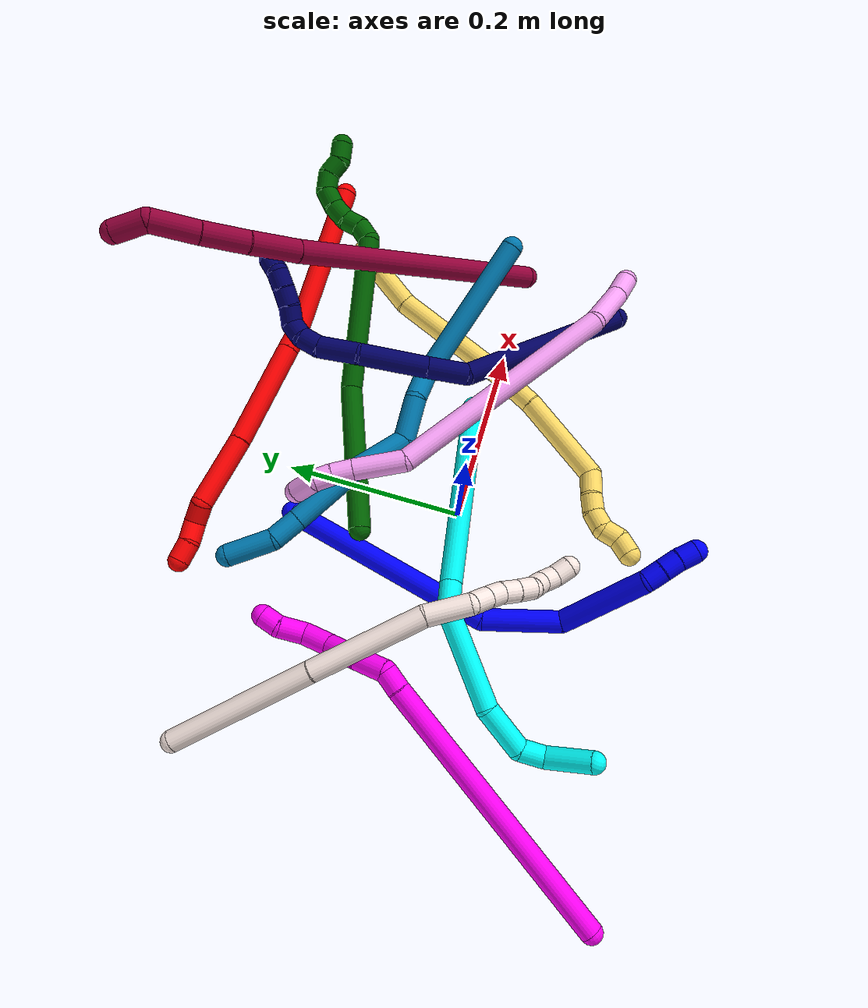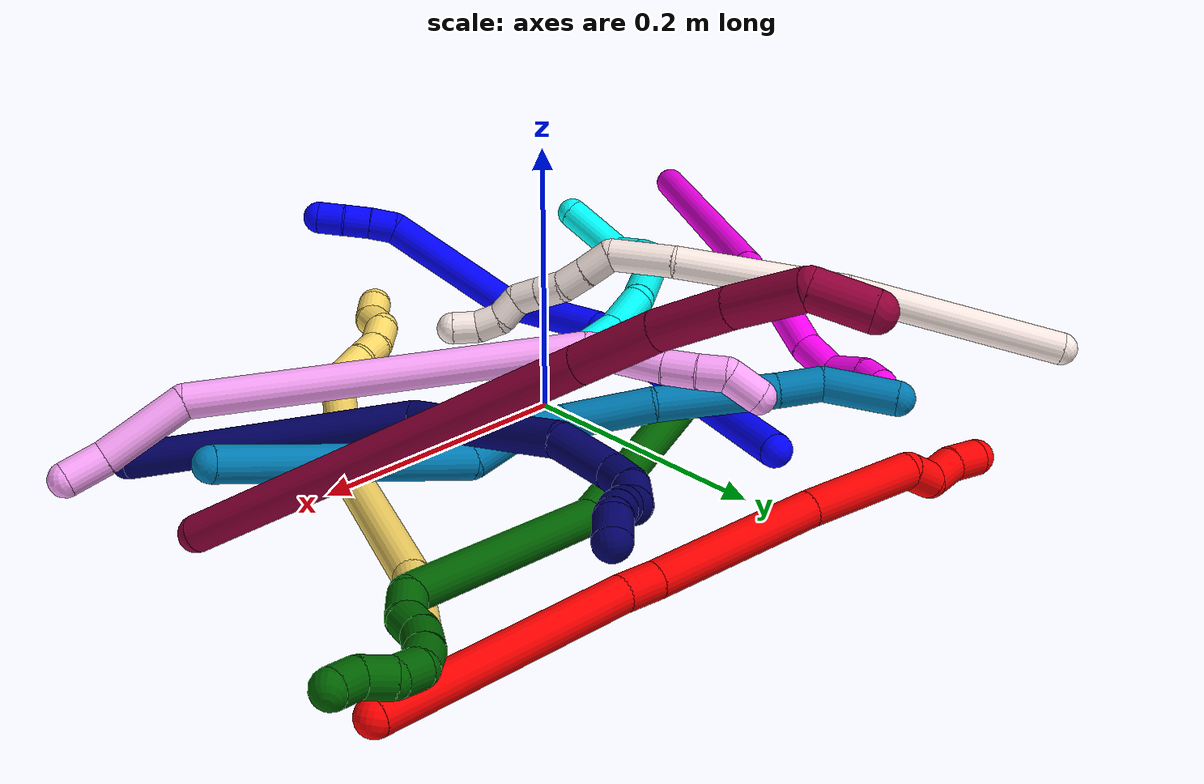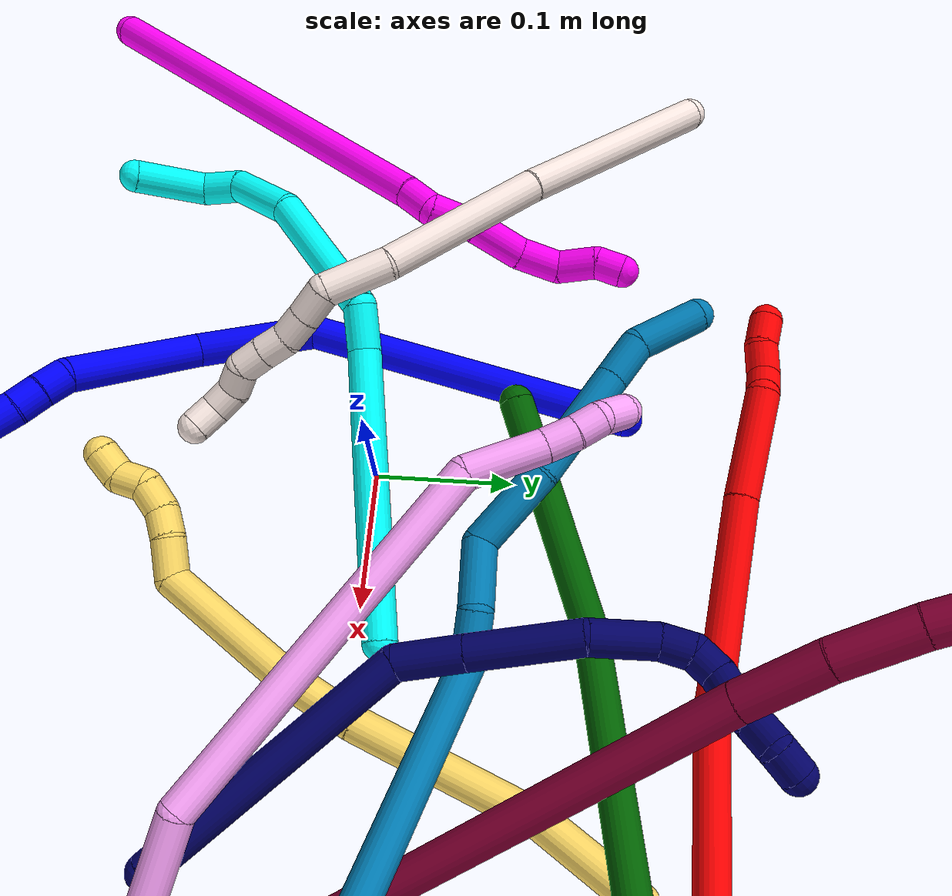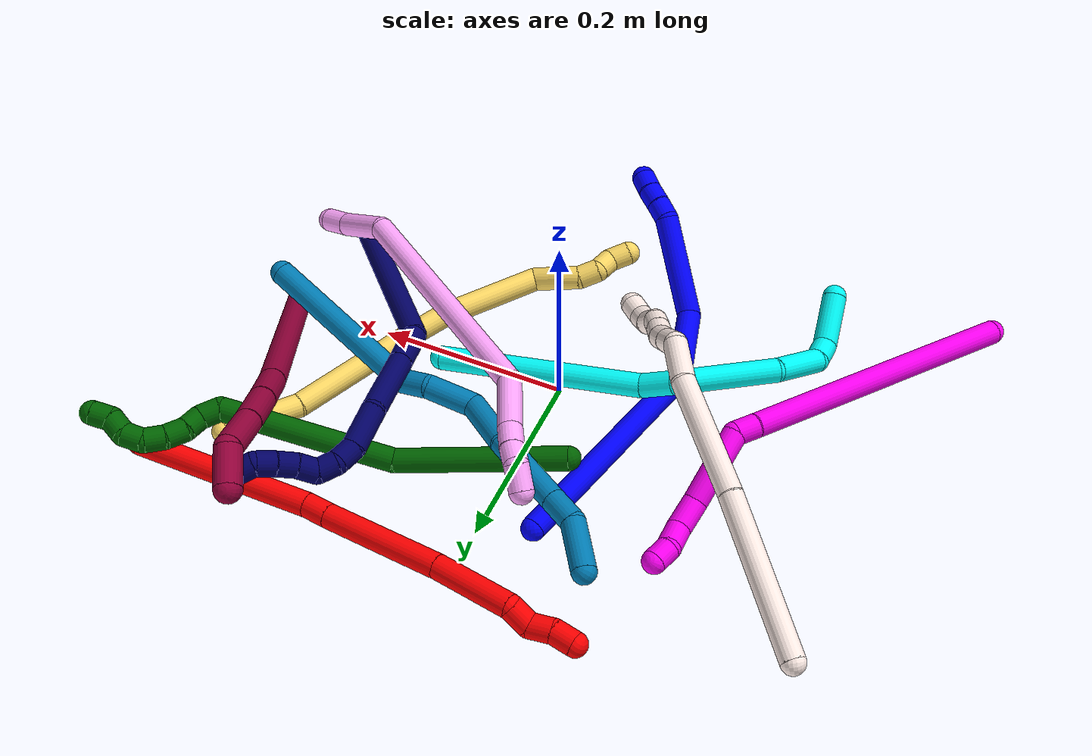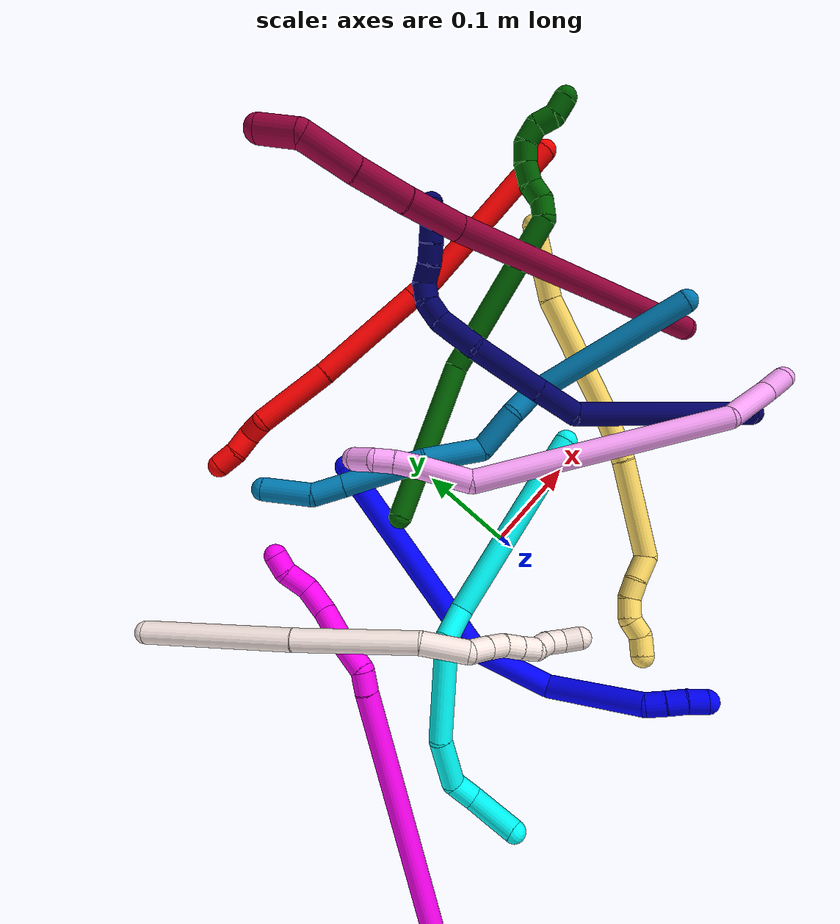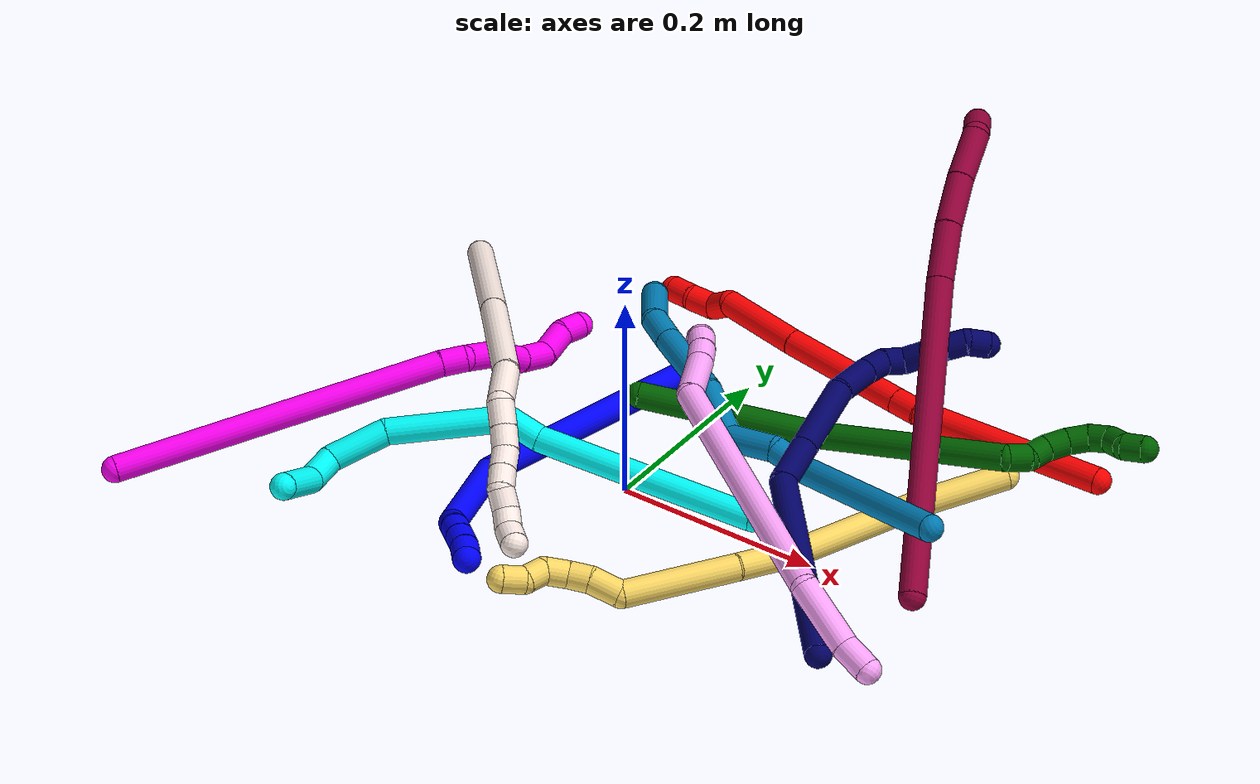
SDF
<sdf version="1.7">
 <world name="default">
  <plugin name="TubeGeneratorPlugin" filename="libtube_generator_plugin.so"/>
  <model name="photoneo_s_sensor">
   <static>1</static>
   <pose>0 0 2 1.57079 1.57079 3.14159</pose>
   <link name="link">
    <inertial><mass>0.1</mass></inertial>
    <sensor name="sensor" type="depth">
     <update_rate>30</update_rate>
     <camera>
      <horizontal_fov>1.22</horizontal_fov>
      <image><width>1920</width><height>1200</height><format>B8G8R8</format></image>
      <clip><near>0.1</near><far>4</far></clip>
      <depth_camera><output>points</output></depth_camera>
     </camera>
     <plugin name="camera_plugin" filename="libgazebo_ros_depth_camera.so">
      <baseline>0.2</baseline>
      <alwaysOn>1</alwaysOn>
      <updateRate>0.0</updateRate>
      <cameraName>camera_ir</cameraName>
      <imageTopicName>/camera/color/image_raw</imageTopicName>
      <cameraInfoTopicName>/camera/color/camera_info</cameraInfoTopicName>
      <depthImageTopicName>/camera/depth/image_raw</depthImageTopicName>
      <depthImageCameraInfoTopicName>/camera/depth/camera_info</depthImageCameraInfoTopicName>
      <pointCloudTopicName>/camera/depth/points</pointCloudTopicName>
      <frameName>fr_optical</frameName>
      <pointCloudCutoff>0.1</pointCloudCutoff>
      <pointCloudCutoffMax>2.0</pointCloudCutoffMax>
      <distortionK1>0</distortionK1>
      <distortionK2>0</distortionK2>
      <distortionK3>0</distortionK3>
      <distortionT1>0</distortionT1>
      <distortionT2>0</distortionT2>
      <CxPrime>0</CxPrime>
      <Cx>0</Cx>
      <Cy>0</Cy>
      <focalLength>0</focalLength>
      <hackBaseline>0</hackBaseline>
     </plugin>
    </sensor>
   </link>
  </model>
  <gravity>0 0 -9.8</gravity>
  <magnetic_field>6e-06 2.3e-05 -4.2e-05</magnetic_field>
  <atmosphere type="adiabatic"/>
  <physics name="default_physics" default="0" type="ode">
   <max_step_size>0.003</max_step_size>
   <real_time_factor>1</real_time_factor>
   <real_time_update_rate>1000</real_time_update_rate>
   <max_contacts>10000</max_contacts>
   <ode>
    <solver>
     <type>quick</type>
     <iters>100</iters>
     <sor>1.3</sor>
     <use_dynamic_moi_rescaling>0</use_dynamic_moi_rescaling>
    </solver>
    <constraints>
     <contact_max_correcting_vel>0</contact_max_correcting_vel>
     <contact_surface_layer>0.001</contact_surface_layer>
     <cfm>0</cfm>
     <erp>0.2</erp>
    </constraints>
   </ode>
  </physics>
  <scene><ambient>0.4 0.4 0.4 1</ambient><background>0.7 0.7 0.7 1</background><shadows>0</shadows></scene>
  <audio><device>default</device></audio>
  <spherical_coordinates>
   <surface_model>EARTH_WGS84</surface_model>
   <latitude_deg>0</latitude_deg>
   <longitude_deg>0</longitude_deg>
   <elevation>0</elevation>
   <heading_deg>0</heading_deg>
  </spherical_coordinates>
  <model name="bin">
   <static>1</static>
   <link name="bottom">
    <collision name="collision-bottom">
     <pose>0 0 -0.01 0 -0 0</pose>
     <geometry><box><size>0.8 0.6 0.02</size></box></geometry>
     <surface>
      <friction><ode><mu>100</mu><mu2>100</mu2></ode></friction>
      <contact><collide_bitmask>65535</collide_bitmask></contact>
     </surface>
    </collision>
   </link>
   <link name="west_wall">
    <collision name="collision-west_wall">
     <pose>-0.41 0 0.1 0 -0 0</pose>
     <geometry><box><size>0.02 0.6 0.2</size></box></geometry>
     <surface>
      <friction><ode><mu>100</mu><mu2>100</mu2></ode></friction>
      <contact><collide_bitmask>65535</collide_bitmask></contact>
     </surface>
    </collision>
   </link>
   <link name="east_wall">
    <collision name="collision-east_wall">
     <pose>0.41 0 0.1 0 -0 0</pose>
     <geometry><box><size>0.02 0.6 0.2</size></box></geometry>
     <surface>
      <friction><ode><mu>100</mu><mu2>100</mu2></ode></friction>
      <contact><collide_bitmask>65535</collide_bitmask></contact>
     </surface>
    </collision>
   </link>
   <link name="south_wall">
    <collision name="collision-south_wall">
     <pose>0 -0.31 0.1 0 -0 0</pose>
     <geometry><box><size>0.8 0.02 0.2</size></box></geometry>
     <surface>
      <friction><ode><mu>100</mu><mu2>100</mu2></ode></friction>
      <contact><collide_bitmask>65535</collide_bitmask></contact>
     </surface>
    </collision>
   </link>
   <link name="north_wall">
    <collision name="collision-north_wall">
     <pose>0 0.31 0.1 0 -0 0</pose>
     <geometry><box><size>0.8 0.02 0.2</size></box></geometry>
     <surface>
      <friction><ode><mu>100</mu><mu2>100</mu2></ode></friction>
      <contact><collide_bitmask>65535</collide_bitmask></contact>
     </surface>
    </collision>
   </link>
  </model>
  <model name="1">
   <static>0</static>
   <link name="1">
    <collision name="collision-cylinder-e_1_1_4">
     <pose>-0.010804 -0.106059 0.059136 1.06215 -0.088735 -0.052142</pose>
     <geometry><cylinder><radius>0.0125</radius><length>0.243822</length></cylinder></geometry>
     <surface>
      <friction><ode><mu>1.16</mu><mu2>1.16</mu2><slip1>0</slip1><slip2>0</slip2></ode></friction>
      <contact><ode><kp>1e+06</kp><kd>1</kd><max_vel>0</max_vel><min_depth>0.001</min_depth></ode></contact>
     </surface>
    </collision>
    <visual name="visual-cylinder-e_1_1_4">
     <pose>-0.010804 -0.106059 0.059136 1.06215 -0.088735 -0.052142</pose>
     <geometry><cylinder><radius>0.0125</radius><length>0.243822</length></cylinder></geometry>
     <material><ambient>0 0 1 1</ambient></material>
    </visual>
    <collision name="collision-cylinder-e_2_4_5">
     <pose>-0.009007 -0.240824 0.149514 0.743119 0.288675 0.113151</pose>
     <geometry><cylinder><radius>0.0125</radius><length>0.088518</length></cylinder></geometry>
     <surface>
      <friction><ode><mu>1.16</mu><mu2>1.16</mu2><slip1>0</slip1><slip2>0</slip2></ode></friction>
      <contact><ode><kp>1e+06</kp><kd>1</kd><max_vel>0</max_vel><min_depth>0.001</min_depth></ode></contact>
     </surface>
    </collision>
    <visual name="visual-cylinder-e_2_4_5">
     <pose>-0.009007 -0.240824 0.149514 0.743119 0.288675 0.113151</pose>
     <geometry><cylinder><radius>0.0125</radius><length>0.088518</length></cylinder></geometry>
     <material><ambient>0 0 1 1</ambient></material>
    </visual>
    <collision name="collision-cylinder-e_3_5_6">
     <pose>0.010606 -0.271583 0.233745 0.038718 0.1315 0.00255</pose>
     <geometry><cylinder><radius>0.0125</radius><length>0.106981</length></cylinder></geometry>
     <surface>
      <friction><ode><mu>1.16</mu><mu2>1.16</mu2><slip1>0</slip1><slip2>0</slip2></ode></friction>
      <contact><ode><kp>1e+06</kp><kd>1</kd><max_vel>0</max_vel><min_depth>0.001</min_depth></ode></contact>
     </surface>
    </collision>
    <visual name="visual-cylinder-e_3_5_6">
     <pose>0.010606 -0.271583 0.233745 0.038718 0.1315 0.00255</pose>
     <geometry><cylinder><radius>0.0125</radius><length>0.106981</length></cylinder></geometry>
     <material><ambient>0 0 1 1</ambient></material>
    </visual>
    <collision name="collision-cylinder-e_4_6_7">
     <pose>0.022781 -0.274605 0.295456 0.110668 0.531647 0.03016</pose>
     <geometry><cylinder><radius>0.0125</radius><length>0.020363</length></cylinder></geometry>
     <surface>
      <friction><ode><mu>1.16</mu><mu2>1.16</mu2><slip1>0</slip1><slip2>0</slip2></ode></friction>
      <contact><ode><kp>1e+06</kp><kd>1</kd><max_vel>0</max_vel><min_depth>0.001</min_depth></ode></contact>
     </surface>
    </collision>
    <visual name="visual-cylinder-e_4_6_7">
     <pose>0.022781 -0.274605 0.295456 0.110668 0.531647 0.03016</pose>
     <geometry><cylinder><radius>0.0125</radius><length>0.020363</length></cylinder></geometry>
     <material><ambient>0 0 1 1</ambient></material>
    </visual>
    <collision name="collision-cylinder-e_5_7_8">
     <pose>0.033707 -0.276838 0.312404 0.15247 0.60582 0.047735</pose>
     <geometry><cylinder><radius>0.0125</radius><length>0.020247</length></cylinder></geometry>
     <surface>
      <friction><ode><mu>1.16</mu><mu2>1.16</mu2><slip1>0</slip1><slip2>0</slip2></ode></friction>
      <contact><ode><kp>1e+06</kp><kd>1</kd><max_vel>0</max_vel><min_depth>0.001</min_depth></ode></contact>
     </surface>
    </collision>
    <visual name="visual-cylinder-e_5_7_8">
     <pose>0.033707 -0.276838 0.312404 0.15247 0.60582 0.047735</pose>
     <geometry><cylinder><radius>0.0125</radius><length>0.020247</length></cylinder></geometry>
     <material><ambient>0 0 1 1</ambient></material>
    </visual>
    <collision name="collision-cylinder-e_6_8_2">
     <pose>0.044937 -0.280638 0.328654 0.306028 0.575875 0.091286</pose>
     <geometry><cylinder><radius>0.0125</radius><length>0.02007</length></cylinder></geometry>
     <surface>
      <friction><ode><mu>1.16</mu><mu2>1.16</mu2><slip1>0</slip1><slip2>0</slip2></ode></friction>
      <contact><ode><kp>1e+06</kp><kd>1</kd><max_vel>0</max_vel><min_depth>0.001</min_depth></ode></contact>
     </surface>
    </collision>
    <visual name="visual-cylinder-e_6_8_2">
     <pose>0.044937 -0.280638 0.328654 0.306028 0.575875 0.091286</pose>
     <geometry><cylinder><radius>0.0125</radius><length>0.02007</length></cylinder></geometry>
     <material><ambient>0 0 1 1</ambient></material>
    </visual>
    <collision name="collision-sphere-2">
     <pose>0.050401 -0.283173 0.33668 0 -0 0</pose>
     <geometry><sphere><radius>0.0125</radius></sphere></geometry>
     <surface>
      <friction><ode><mu>1.16</mu><mu2>1.16</mu2><slip1>0</slip1><slip2>0</slip2></ode></friction>
      <contact><ode><kp>1e+06</kp><kd>1</kd><max_vel>0</max_vel><min_depth>0.001</min_depth></ode></contact>
     </surface>
    </collision>
    <visual name="visual-sphere-2">
     <pose>0.050401 -0.283173 0.33668 0 -0 0</pose>
     <geometry><sphere><radius>0.0125</radius></sphere></geometry>
     <material><ambient>0 0 1 1</ambient></material>
    </visual>
    <collision name="collision-sphere-4">
     <pose>-0.021607 -0.212118 0.118272 0 -0 0</pose>
     <geometry><sphere><radius>0.0125</radius></sphere></geometry>
     <surface>
      <friction><ode><mu>1.16</mu><mu2>1.16</mu2><slip1>0</slip1><slip2>0</slip2></ode></friction>
      <contact><ode><kp>1e+06</kp><kd>1</kd><max_vel>0</max_vel><min_depth>0.001</min_depth></ode></contact>
     </surface>
    </collision>
    <visual name="visual-sphere-4">
     <pose>-0.021607 -0.212118 0.118272 0 -0 0</pose>
     <geometry><sphere><radius>0.0125</radius></sphere></geometry>
     <material><ambient>0 0 1 1</ambient></material>
    </visual>
    <collision name="collision-sphere-1">
     <geometry><sphere><radius>0.0125</radius></sphere></geometry>
     <surface>
      <friction><ode><mu>1.16</mu><mu2>1.16</mu2><slip1>0</slip1><slip2>0</slip2></ode></friction>
      <contact><ode><kp>1e+06</kp><kd>1</kd><max_vel>0</max_vel><min_depth>0.001</min_depth></ode></contact>
     </surface>
    </collision>
    <visual name="visual-sphere-1">
     <geometry><sphere><radius>0.0125</radius></sphere></geometry>
     <material><ambient>0 0 1 1</ambient></material>
    </visual>
    <collision name="collision-sphere-8">
     <pose>0.039472 -0.278102 0.320629 0 -0 0</pose>
     <geometry><sphere><radius>0.0125</radius></sphere></geometry>
     <surface>
      <friction><ode><mu>1.16</mu><mu2>1.16</mu2><slip1>0</slip1><slip2>0</slip2></ode></friction>
      <contact><ode><kp>1e+06</kp><kd>1</kd><max_vel>0</max_vel><min_depth>0.001</min_depth></ode></contact>
     </surface>
    </collision>
    <visual name="visual-sphere-8">
     <pose>0.039472 -0.278102 0.320629 0 -0 0</pose>
     <geometry><sphere><radius>0.0125</radius></sphere></geometry>
     <material><ambient>0 0 1 1</ambient></material>
    </visual>
    <collision name="collision-sphere-5">
     <pose>0.003592 -0.269531 0.180757 0 -0 0</pose>
     <geometry><sphere><radius>0.0125</radius></sphere></geometry>
     <surface>
      <friction><ode><mu>1.16</mu><mu2>1.16</mu2><slip1>0</slip1><slip2>0</slip2></ode></friction>
      <contact><ode><kp>1e+06</kp><kd>1</kd><max_vel>0</max_vel><min_depth>0.001</min_depth></ode></contact>
     </surface>
    </collision>
    <visual name="visual-sphere-5">
     <pose>0.003592 -0.269531 0.180757 0 -0 0</pose>
     <geometry><sphere><radius>0.0125</radius></sphere></geometry>
     <material><ambient>0 0 1 1</ambient></material>
    </visual>
    <collision name="collision-sphere-6">
     <pose>0.01762 -0.273636 0.286734 0 -0 0</pose>
     <geometry><sphere><radius>0.0125</radius></sphere></geometry>
     <surface>
      <friction><ode><mu>1.16</mu><mu2>1.16</mu2><slip1>0</slip1><slip2>0</slip2></ode></friction>
      <contact><ode><kp>1e+06</kp><kd>1</kd><max_vel>0</max_vel><min_depth>0.001</min_depth></ode></contact>
     </surface>
    </collision>
    <visual name="visual-sphere-6">
     <pose>0.01762 -0.273636 0.286734 0 -0 0</pose>
     <geometry><sphere><radius>0.0125</radius></sphere></geometry>
     <material><ambient>0 0 1 1</ambient></material>
    </visual>
    <collision name="collision-sphere-7">
     <pose>0.027943 -0.275574 0.304179 0 -0 0</pose>
     <geometry><sphere><radius>0.0125</radius></sphere></geometry>
     <surface>
      <friction><ode><mu>1.16</mu><mu2>1.16</mu2><slip1>0</slip1><slip2>0</slip2></ode></friction>
      <contact><ode><kp>1e+06</kp><kd>1</kd><max_vel>0</max_vel><min_depth>0.001</min_depth></ode></contact>
     </surface>
    </collision>
    <visual name="visual-sphere-7">
     <pose>0.027943 -0.275574 0.304179 0 -0 0</pose>
     <geometry><sphere><radius>0.0125</radius></sphere></geometry>
     <material><ambient>0 0 1 1</ambient></material>
    </visual>
    <inertial>
     <pose>-0.000497 -0.18612 0.143194 0 -0 0</pose>
     <mass>0.5</mass>
     <inertia>
      <ixx>0.001326</ixx>
      <ixy>0</ixy>
      <ixz>0</ixz>
      <iyy>0.000675</iyy>
      <iyz>0</iyz>
      <izz>0.001204</izz>
     </inertia>
    </inertial>
   </link>
   <pose>-0.052392 0.179454 0.011462 0.576975 0.656206 -0.124344</pose>
  </model>
  <model name="2">
   <static>0</static>
   <link name="2">
    <collision name="collision-cylinder-e_1_1_4">
     <pose>-0.081444 0.021809 0.044616 -0.454664 -1.02323 0.258329</pose>
     <geometry><cylinder><radius>0.0125</radius><length>0.190781</length></cylinder></geometry>
     <surface>
      <friction><ode><mu>1.16</mu><mu2>1.16</mu2><slip1>0</slip1><slip2>0</slip2></ode></friction>
      <contact><ode><kp>1e+06</kp><kd>1</kd><max_vel>0</max_vel><min_depth>0.001</min_depth></ode></contact>
     </surface>
    </collision>
    <visual name="visual-cylinder-e_1_1_4">
     <pose>-0.081444 0.021809 0.044616 -0.454664 -1.02323 0.258329</pose>
     <geometry><cylinder><radius>0.0125</radius><length>0.190781</length></cylinder></geometry>
     <material><ambient>1 0 0 1</ambient></material>
    </visual>
    <collision name="collision-cylinder-e_2_4_5">
     <pose>-0.173365 0.04847 0.095147 -0.686949 -0.940199 0.359516</pose>
     <geometry><cylinder><radius>0.0125</radius><length>0.025947</length></cylinder></geometry>
     <surface>
      <friction><ode><mu>1.16</mu><mu2>1.16</mu2><slip1>0</slip1><slip2>0</slip2></ode></friction>
      <contact><ode><kp>1e+06</kp><kd>1</kd><max_vel>0</max_vel><min_depth>0.001</min_depth></ode></contact>
     </surface>
    </collision>
    <visual name="visual-cylinder-e_2_4_5">
     <pose>-0.173365 0.04847 0.095147 -0.686949 -0.940199 0.359516</pose>
     <geometry><cylinder><radius>0.0125</radius><length>0.025947</length></cylinder></geometry>
     <material><ambient>1 0 0 1</ambient></material>
    </visual>
    <collision name="collision-cylinder-e_3_5_6">
     <pose>-0.234068 0.075944 0.132165 -0.628837 -0.91728 0.318427</pose>
     <geometry><cylinder><radius>0.0125</radius><length>0.126518</length></cylinder></geometry>
     <surface>
      <friction><ode><mu>1.16</mu><mu2>1.16</mu2><slip1>0</slip1><slip2>0</slip2></ode></friction>
      <contact><ode><kp>1e+06</kp><kd>1</kd><max_vel>0</max_vel><min_depth>0.001</min_depth></ode></contact>
     </surface>
    </collision>
    <visual name="visual-cylinder-e_3_5_6">
     <pose>-0.234068 0.075944 0.132165 -0.628837 -0.91728 0.318427</pose>
     <geometry><cylinder><radius>0.0125</radius><length>0.126518</length></cylinder></geometry>
     <material><ambient>1 0 0 1</ambient></material>
    </visual>
    <collision name="collision-cylinder-e_4_6_7">
     <pose>-0.317243 0.115919 0.182506 -0.733906 -0.904481 0.36921</pose>
     <geometry><cylinder><radius>0.0125</radius><length>0.083831</length></cylinder></geometry>
     <surface>
      <friction><ode><mu>1.16</mu><mu2>1.16</mu2><slip1>0</slip1><slip2>0</slip2></ode></friction>
      <contact><ode><kp>1e+06</kp><kd>1</kd><max_vel>0</max_vel><min_depth>0.001</min_depth></ode></contact>
     </surface>
    </collision>
    <visual name="visual-cylinder-e_4_6_7">
     <pose>-0.317243 0.115919 0.182506 -0.733906 -0.904481 0.36921</pose>
     <geometry><cylinder><radius>0.0125</radius><length>0.083831</length></cylinder></geometry>
     <material><ambient>1 0 0 1</ambient></material>
    </visual>
    <collision name="collision-cylinder-e_5_7_8">
     <pose>-0.362173 0.136264 0.200426 -1.98583 -1.30427 1.72789</pose>
     <geometry><cylinder><radius>0.0125</radius><length>0.024837</length></cylinder></geometry>
     <surface>
      <friction><ode><mu>1.16</mu><mu2>1.16</mu2><slip1>0</slip1><slip2>0</slip2></ode></friction>
      <contact><ode><kp>1e+06</kp><kd>1</kd><max_vel>0</max_vel><min_depth>0.001</min_depth></ode></contact>
     </surface>
    </collision>
    <visual name="visual-cylinder-e_5_7_8">
     <pose>-0.362173 0.136264 0.200426 -1.98583 -1.30427 1.72789</pose>
     <geometry><cylinder><radius>0.0125</radius><length>0.024837</length></cylinder></geometry>
     <material><ambient>1 0 0 1</ambient></material>
    </visual>
    <collision name="collision-cylinder-e_6_8_9">
     <pose>-0.384061 0.141376 0.206164 -0.291709 -0.931388 0.147383</pose>
     <geometry><cylinder><radius>0.0125</radius><length>0.024695</length></cylinder></geometry>
     <surface>
      <friction><ode><mu>1.16</mu><mu2>1.16</mu2><slip1>0</slip1><slip2>0</slip2></ode></friction>
      <contact><ode><kp>1e+06</kp><kd>1</kd><max_vel>0</max_vel><min_depth>0.001</min_depth></ode></contact>
     </surface>
    </collision>
    <visual name="visual-cylinder-e_6_8_9">
     <pose>-0.384061 0.141376 0.206164 -0.291709 -0.931388 0.147383</pose>
     <geometry><cylinder><radius>0.0125</radius><length>0.024695</length></cylinder></geometry>
     <material><ambient>1 0 0 1</ambient></material>
    </visual>
    <collision name="collision-cylinder-e_7_9_2">
     <pose>-0.403821 0.148087 0.217539 -0.816126 -1.0016 0.464718</pose>
     <geometry><cylinder><radius>0.0125</radius><length>0.023391</length></cylinder></geometry>
     <surface>
      <friction><ode><mu>1.16</mu><mu2>1.16</mu2><slip1>0</slip1><slip2>0</slip2></ode></friction>
      <contact><ode><kp>1e+06</kp><kd>1</kd><max_vel>0</max_vel><min_depth>0.001</min_depth></ode></contact>
     </surface>
    </collision>
    <visual name="visual-cylinder-e_7_9_2">
     <pose>-0.403821 0.148087 0.217539 -0.816126 -1.0016 0.464718</pose>
     <geometry><cylinder><radius>0.0125</radius><length>0.023391</length></cylinder></geometry>
     <material><ambient>1 0 0 1</ambient></material>
    </visual>
    <collision name="collision-sphere-2">
     <pose>-0.413673 0.152679 0.221857 0 -0 0</pose>
     <geometry><sphere><radius>0.0125</radius></sphere></geometry>
     <surface>
      <friction><ode><mu>1.16</mu><mu2>1.16</mu2><slip1>0</slip1><slip2>0</slip2></ode></friction>
      <contact><ode><kp>1e+06</kp><kd>1</kd><max_vel>0</max_vel><min_depth>0.001</min_depth></ode></contact>
     </surface>
    </collision>
    <visual name="visual-sphere-2">
     <pose>-0.413673 0.152679 0.221857 0 -0 0</pose>
     <geometry><sphere><radius>0.0125</radius></sphere></geometry>
     <material><ambient>1 0 0 1</ambient></material>
    </visual>
    <collision name="collision-sphere-9">
     <pose>-0.39397 0.143495 0.21322 0 -0 0</pose>
     <geometry><sphere><radius>0.0125</radius></sphere></geometry>
     <surface>
      <friction><ode><mu>1.16</mu><mu2>1.16</mu2><slip1>0</slip1><slip2>0</slip2></ode></friction>
      <contact><ode><kp>1e+06</kp><kd>1</kd><max_vel>0</max_vel><min_depth>0.001</min_depth></ode></contact>
     </surface>
    </collision>
    <visual name="visual-sphere-9">
     <pose>-0.39397 0.143495 0.21322 0 -0 0</pose>
     <geometry><sphere><radius>0.0125</radius></sphere></geometry>
     <material><ambient>1 0 0 1</ambient></material>
    </visual>
    <collision name="collision-sphere-4">
     <pose>-0.162887 0.043619 0.089232 0 -0 0</pose>
     <geometry><sphere><radius>0.0125</radius></sphere></geometry>
     <surface>
      <friction><ode><mu>1.16</mu><mu2>1.16</mu2><slip1>0</slip1><slip2>0</slip2></ode></friction>
      <contact><ode><kp>1e+06</kp><kd>1</kd><max_vel>0</max_vel><min_depth>0.001</min_depth></ode></contact>
     </surface>
    </collision>
    <visual name="visual-sphere-4">
     <pose>-0.162887 0.043619 0.089232 0 -0 0</pose>
     <geometry><sphere><radius>0.0125</radius></sphere></geometry>
     <material><ambient>1 0 0 1</ambient></material>
    </visual>
    <collision name="collision-sphere-1">
     <geometry><sphere><radius>0.0125</radius></sphere></geometry>
     <surface>
      <friction><ode><mu>1.16</mu><mu2>1.16</mu2><slip1>0</slip1><slip2>0</slip2></ode></friction>
      <contact><ode><kp>1e+06</kp><kd>1</kd><max_vel>0</max_vel><min_depth>0.001</min_depth></ode></contact>
     </surface>
    </collision>
    <visual name="visual-sphere-1">
     <geometry><sphere><radius>0.0125</radius></sphere></geometry>
     <material><ambient>1 0 0 1</ambient></material>
    </visual>
    <collision name="collision-sphere-8">
     <pose>-0.374153 0.139257 0.199107 0 -0 0</pose>
     <geometry><sphere><radius>0.0125</radius></sphere></geometry>
     <surface>
      <friction><ode><mu>1.16</mu><mu2>1.16</mu2><slip1>0</slip1><slip2>0</slip2></ode></friction>
      <contact><ode><kp>1e+06</kp><kd>1</kd><max_vel>0</max_vel><min_depth>0.001</min_depth></ode></contact>
     </surface>
    </collision>
    <visual name="visual-sphere-8">
     <pose>-0.374153 0.139257 0.199107 0 -0 0</pose>
     <geometry><sphere><radius>0.0125</radius></sphere></geometry>
     <material><ambient>1 0 0 1</ambient></material>
    </visual>
    <collision name="collision-sphere-5">
     <pose>-0.183844 0.053321 0.101061 0 -0 0</pose>
     <geometry><sphere><radius>0.0125</radius></sphere></geometry>
     <surface>
      <friction><ode><mu>1.16</mu><mu2>1.16</mu2><slip1>0</slip1><slip2>0</slip2></ode></friction>
      <contact><ode><kp>1e+06</kp><kd>1</kd><max_vel>0</max_vel><min_depth>0.001</min_depth></ode></contact>
     </surface>
    </collision>
    <visual name="visual-sphere-5">
     <pose>-0.183844 0.053321 0.101061 0 -0 0</pose>
     <geometry><sphere><radius>0.0125</radius></sphere></geometry>
     <material><ambient>1 0 0 1</ambient></material>
    </visual>
    <collision name="collision-sphere-6">
     <pose>-0.284293 0.098566 0.163268 0 -0 0</pose>
     <geometry><sphere><radius>0.0125</radius></sphere></geometry>
     <surface>
      <friction><ode><mu>1.16</mu><mu2>1.16</mu2><slip1>0</slip1><slip2>0</slip2></ode></friction>
      <contact><ode><kp>1e+06</kp><kd>1</kd><max_vel>0</max_vel><min_depth>0.001</min_depth></ode></contact>
     </surface>
    </collision>
    <visual name="visual-sphere-6">
     <pose>-0.284293 0.098566 0.163268 0 -0 0</pose>
     <geometry><sphere><radius>0.0125</radius></sphere></geometry>
     <material><ambient>1 0 0 1</ambient></material>
    </visual>
    <collision name="collision-sphere-7">
     <pose>-0.350193 0.133271 0.201744 0 -0 0</pose>
     <geometry><sphere><radius>0.0125</radius></sphere></geometry>
     <surface>
      <friction><ode><mu>1.16</mu><mu2>1.16</mu2><slip1>0</slip1><slip2>0</slip2></ode></friction>
      <contact><ode><kp>1e+06</kp><kd>1</kd><max_vel>0</max_vel><min_depth>0.001</min_depth></ode></contact>
     </surface>
    </collision>
    <visual name="visual-sphere-7">
     <pose>-0.350193 0.133271 0.201744 0 -0 0</pose>
     <geometry><sphere><radius>0.0125</radius></sphere></geometry>
     <material><ambient>1 0 0 1</ambient></material>
    </visual>
    <inertial>
     <pose>-0.208341 0.070168 0.116319 0 -0 0</pose>
     <mass>0.5</mass>
     <inertia>
      <ixx>0.000521</ixx>
      <ixy>0</ixy>
      <ixz>0</ixz>
      <iyy>0.000915</iyy>
      <iyz>0</iyz>
      <izz>0.000484</izz>
     </inertia>
    </inertial>
   </link>
   <pose>0.34993 0.243327 0.012501 0.189153 -0.53649 0.138691</pose>
  </model>
  <model name="3">
   <static>0</static>
   <link name="3">
    <collision name="collision-cylinder-e_1_1_4">
     <pose>-0.056237 -0.037152 0.083203 0.419963 -0.552947 -0.120796</pose>
     <geometry><cylinder><radius>0.0125</radius><length>0.214155</length></cylinder></geometry>
     <surface>
      <friction><ode><mu>1.16</mu><mu2>1.16</mu2><slip1>0</slip1><slip2>0</slip2></ode></friction>
      <contact><ode><kp>1e+06</kp><kd>1</kd><max_vel>0</max_vel><min_depth>0.001</min_depth></ode></contact>
     </surface>
    </collision>
    <visual name="visual-cylinder-e_1_1_4">
     <pose>-0.056237 -0.037152 0.083203 0.419963 -0.552947 -0.120796</pose>
     <geometry><cylinder><radius>0.0125</radius><length>0.214155</length></cylinder></geometry>
     <material><ambient>0.003922 1 0.996078 1</ambient></material>
    </visual>
    <collision name="collision-cylinder-e_2_4_5">
     <pose>-0.123277 -0.083573 0.176278 0.75385 -0.673382 -0.275357</pose>
     <geometry><cylinder><radius>0.0125</radius><length>0.034646</length></cylinder></geometry>
     <surface>
      <friction><ode><mu>1.16</mu><mu2>1.16</mu2><slip1>0</slip1><slip2>0</slip2></ode></friction>
      <contact><ode><kp>1e+06</kp><kd>1</kd><max_vel>0</max_vel><min_depth>0.001</min_depth></ode></contact>
     </surface>
    </collision>
    <visual name="visual-cylinder-e_2_4_5">
     <pose>-0.123277 -0.083573 0.176278 0.75385 -0.673382 -0.275357</pose>
     <geometry><cylinder><radius>0.0125</radius><length>0.034646</length></cylinder></geometry>
     <material><ambient>0.003922 1 0.996078 1</ambient></material>
    </visual>
    <collision name="collision-cylinder-e_3_5_6">
     <pose>-0.176732 -0.086949 0.221127 -0.166906 -0.877089 0.078421</pose>
     <geometry><cylinder><radius>0.0125</radius><length>0.110948</length></cylinder></geometry>
     <surface>
      <friction><ode><mu>1.16</mu><mu2>1.16</mu2><slip1>0</slip1><slip2>0</slip2></ode></friction>
      <contact><ode><kp>1e+06</kp><kd>1</kd><max_vel>0</max_vel><min_depth>0.001</min_depth></ode></contact>
     </surface>
    </collision>
    <visual name="visual-cylinder-e_3_5_6">
     <pose>-0.176732 -0.086949 0.221127 -0.166906 -0.877089 0.078421</pose>
     <geometry><cylinder><radius>0.0125</radius><length>0.110948</length></cylinder></geometry>
     <material><ambient>0.003922 1 0.996078 1</ambient></material>
    </visual>
    <collision name="collision-cylinder-e_4_6_7">
     <pose>-0.240422 -0.068561 0.269574 -0.747864 -0.852887 0.35284</pose>
     <geometry><cylinder><radius>0.0125</radius><length>0.055862</length></cylinder></geometry>
     <surface>
      <friction><ode><mu>1.16</mu><mu2>1.16</mu2><slip1>0</slip1><slip2>0</slip2></ode></friction>
      <contact><ode><kp>1e+06</kp><kd>1</kd><max_vel>0</max_vel><min_depth>0.001</min_depth></ode></contact>
     </surface>
    </collision>
    <visual name="visual-cylinder-e_4_6_7">
     <pose>-0.240422 -0.068561 0.269574 -0.747864 -0.852887 0.35284</pose>
     <geometry><cylinder><radius>0.0125</radius><length>0.055862</length></cylinder></geometry>
     <material><ambient>0.003922 1 0.996078 1</ambient></material>
    </visual>
    <collision name="collision-cylinder-e_5_7_8">
     <pose>-0.272516 -0.046208 0.282237 -1.65256 -0.840951 0.903614</pose>
     <geometry><cylinder><radius>0.0125</radius><length>0.029669</length></cylinder></geometry>
     <surface>
      <friction><ode><mu>1.16</mu><mu2>1.16</mu2><slip1>0</slip1><slip2>0</slip2></ode></friction>
      <contact><ode><kp>1e+06</kp><kd>1</kd><max_vel>0</max_vel><min_depth>0.001</min_depth></ode></contact>
     </surface>
    </collision>
    <visual name="visual-cylinder-e_5_7_8">
     <pose>-0.272516 -0.046208 0.282237 -1.65256 -0.840951 0.903614</pose>
     <geometry><cylinder><radius>0.0125</radius><length>0.029669</length></cylinder></geometry>
     <material><ambient>0.003922 1 0.996078 1</ambient></material>
    </visual>
    <collision name="collision-cylinder-e_6_8_2">
     <pose>-0.30722 -0.031866 0.268421 -2.80966 -1.04386 2.57477</pose>
     <geometry><cylinder><radius>0.0125</radius><length>0.05472</length></cylinder></geometry>
     <surface>
      <friction><ode><mu>1.16</mu><mu2>1.16</mu2><slip1>0</slip1><slip2>0</slip2></ode></friction>
      <contact><ode><kp>1e+06</kp><kd>1</kd><max_vel>0</max_vel><min_depth>0.001</min_depth></ode></contact>
     </surface>
    </collision>
    <visual name="visual-cylinder-e_6_8_2">
     <pose>-0.30722 -0.031866 0.268421 -2.80966 -1.04386 2.57477</pose>
     <geometry><cylinder><radius>0.0125</radius><length>0.05472</length></cylinder></geometry>
     <material><ambient>0.003922 1 0.996078 1</ambient></material>
    </visual>
    <collision name="collision-sphere-2">
     <pose>-0.330869 -0.027383 0.255413 0 -0 0</pose>
     <geometry><sphere><radius>0.0125</radius></sphere></geometry>
     <surface>
      <friction><ode><mu>1.16</mu><mu2>1.16</mu2><slip1>0</slip1><slip2>0</slip2></ode></friction>
      <contact><ode><kp>1e+06</kp><kd>1</kd><max_vel>0</max_vel><min_depth>0.001</min_depth></ode></contact>
     </surface>
    </collision>
    <visual name="visual-sphere-2">
     <pose>-0.330869 -0.027383 0.255413 0 -0 0</pose>
     <geometry><sphere><radius>0.0125</radius></sphere></geometry>
     <material><ambient>0.003922 1 0.996078 1</ambient></material>
    </visual>
    <collision name="collision-sphere-4">
     <pose>-0.112474 -0.074305 0.166406 0 -0 0</pose>
     <geometry><sphere><radius>0.0125</radius></sphere></geometry>
     <surface>
      <friction><ode><mu>1.16</mu><mu2>1.16</mu2><slip1>0</slip1><slip2>0</slip2></ode></friction>
      <contact><ode><kp>1e+06</kp><kd>1</kd><max_vel>0</max_vel><min_depth>0.001</min_depth></ode></contact>
     </surface>
    </collision>
    <visual name="visual-sphere-4">
     <pose>-0.112474 -0.074305 0.166406 0 -0 0</pose>
     <geometry><sphere><radius>0.0125</radius></sphere></geometry>
     <material><ambient>0.003922 1 0.996078 1</ambient></material>
    </visual>
    <collision name="collision-sphere-1">
     <geometry><sphere><radius>0.0125</radius></sphere></geometry>
     <surface>
      <friction><ode><mu>1.16</mu><mu2>1.16</mu2><slip1>0</slip1><slip2>0</slip2></ode></friction>
      <contact><ode><kp>1e+06</kp><kd>1</kd><max_vel>0</max_vel><min_depth>0.001</min_depth></ode></contact>
     </surface>
    </collision>
    <visual name="visual-sphere-1">
     <geometry><sphere><radius>0.0125</radius></sphere></geometry>
     <material><ambient>0.003922 1 0.996078 1</ambient></material>
    </visual>
    <collision name="collision-sphere-8">
     <pose>-0.283571 -0.03635 0.281429 0 -0 0</pose>
     <geometry><sphere><radius>0.0125</radius></sphere></geometry>
     <surface>
      <friction><ode><mu>1.16</mu><mu2>1.16</mu2><slip1>0</slip1><slip2>0</slip2></ode></friction>
      <contact><ode><kp>1e+06</kp><kd>1</kd><max_vel>0</max_vel><min_depth>0.001</min_depth></ode></contact>
     </surface>
    </collision>
    <visual name="visual-sphere-8">
     <pose>-0.283571 -0.03635 0.281429 0 -0 0</pose>
     <geometry><sphere><radius>0.0125</radius></sphere></geometry>
     <material><ambient>0.003922 1 0.996078 1</ambient></material>
    </visual>
    <collision name="collision-sphere-5">
     <pose>-0.13408 -0.092842 0.186151 0 -0 0</pose>
     <geometry><sphere><radius>0.0125</radius></sphere></geometry>
     <surface>
      <friction><ode><mu>1.16</mu><mu2>1.16</mu2><slip1>0</slip1><slip2>0</slip2></ode></friction>
      <contact><ode><kp>1e+06</kp><kd>1</kd><max_vel>0</max_vel><min_depth>0.001</min_depth></ode></contact>
     </surface>
    </collision>
    <visual name="visual-sphere-5">
     <pose>-0.13408 -0.092842 0.186151 0 -0 0</pose>
     <geometry><sphere><radius>0.0125</radius></sphere></geometry>
     <material><ambient>0.003922 1 0.996078 1</ambient></material>
    </visual>
    <collision name="collision-sphere-6">
     <pose>-0.219385 -0.081057 0.256104 0 -0 0</pose>
     <geometry><sphere><radius>0.0125</radius></sphere></geometry>
     <surface>
      <friction><ode><mu>1.16</mu><mu2>1.16</mu2><slip1>0</slip1><slip2>0</slip2></ode></friction>
      <contact><ode><kp>1e+06</kp><kd>1</kd><max_vel>0</max_vel><min_depth>0.001</min_depth></ode></contact>
     </surface>
    </collision>
    <visual name="visual-sphere-6">
     <pose>-0.219385 -0.081057 0.256104 0 -0 0</pose>
     <geometry><sphere><radius>0.0125</radius></sphere></geometry>
     <material><ambient>0.003922 1 0.996078 1</ambient></material>
    </visual>
    <collision name="collision-sphere-7">
     <pose>-0.26146 -0.056066 0.283045 0 -0 0</pose>
     <geometry><sphere><radius>0.0125</radius></sphere></geometry>
     <surface>
      <friction><ode><mu>1.16</mu><mu2>1.16</mu2><slip1>0</slip1><slip2>0</slip2></ode></friction>
      <contact><ode><kp>1e+06</kp><kd>1</kd><max_vel>0</max_vel><min_depth>0.001</min_depth></ode></contact>
     </surface>
    </collision>
    <visual name="visual-sphere-7">
     <pose>-0.26146 -0.056066 0.283045 0 -0 0</pose>
     <geometry><sphere><radius>0.0125</radius></sphere></geometry>
     <material><ambient>0.003922 1 0.996078 1</ambient></material>
    </visual>
    <inertial>
     <pose>-0.148499 -0.054887 0.17316 0 -0 0</pose>
     <mass>0.5</mass>
     <inertia>
      <ixx>0.000686</ixx>
      <ixy>0</ixy>
      <ixz>0</ixz>
      <iyy>0.000851</iyy>
      <iyz>0</iyz>
      <izz>0.000841</izz>
     </inertia>
    </inertial>
   </link>
   <pose>0.126271 0.017504 0.011819 -2.13149 0.396029 1.16094</pose>
  </model>
  <model name="4">
   <static>0</static>
   <link name="4">
    <collision name="collision-cylinder-e_1_1_4">
     <pose>0.008783 0.009709 -0.006749 -2.17822 0.638866 -1.12827</pose>
     <geometry><cylinder><radius>0.0125</radius><length>0.029458</length></cylinder></geometry>
     <surface>
      <friction><ode><mu>1.16</mu><mu2>1.16</mu2><slip1>0</slip1><slip2>0</slip2></ode></friction>
      <contact><ode><kp>1e+06</kp><kd>1</kd><max_vel>0</max_vel><min_depth>0.001</min_depth></ode></contact>
     </surface>
    </collision>
    <visual name="visual-cylinder-e_1_1_4">
     <pose>0.008783 0.009709 -0.006749 -2.17822 0.638866 -1.12827</pose>
     <geometry><cylinder><radius>0.0125</radius><length>0.029458</length></cylinder></geometry>
     <material><ambient>1 0.65098 0.996078 1</ambient></material>
    </visual>
    <collision name="collision-cylinder-e_2_4_5">
     <pose>0.038702 0.035855 -0.031743 -2.4083 0.710669 -1.53657</pose>
     <geometry><cylinder><radius>0.0125</radius><length>0.064804</length></cylinder></geometry>
     <surface>
      <friction><ode><mu>1.16</mu><mu2>1.16</mu2><slip1>0</slip1><slip2>0</slip2></ode></friction>
      <contact><ode><kp>1e+06</kp><kd>1</kd><max_vel>0</max_vel><min_depth>0.001</min_depth></ode></contact>
     </surface>
    </collision>
    <visual name="visual-cylinder-e_2_4_5">
     <pose>0.038702 0.035855 -0.031743 -2.4083 0.710669 -1.53657</pose>
     <geometry><cylinder><radius>0.0125</radius><length>0.064804</length></cylinder></geometry>
     <material><ambient>1 0.65098 0.996078 1</ambient></material>
    </visual>
    <collision name="collision-cylinder-e_3_5_6">
     <pose>0.089737 0.152449 -0.140969 -2.30822 0.21746 -0.483611</pose>
     <geometry><cylinder><radius>0.0125</radius><length>0.277147</length></cylinder></geometry>
     <surface>
      <friction><ode><mu>1.16</mu><mu2>1.16</mu2><slip1>0</slip1><slip2>0</slip2></ode></friction>
      <contact><ode><kp>1e+06</kp><kd>1</kd><max_vel>0</max_vel><min_depth>0.001</min_depth></ode></contact>
     </surface>
    </collision>
    <visual name="visual-cylinder-e_3_5_6">
     <pose>0.089737 0.152449 -0.140969 -2.30822 0.21746 -0.483611</pose>
     <geometry><cylinder><radius>0.0125</radius><length>0.277147</length></cylinder></geometry>
     <material><ambient>1 0.65098 0.996078 1</ambient></material>
    </visual>
    <collision name="collision-cylinder-e_4_6_7">
     <pose>0.112994 0.26711 -0.256147 -2.60164 -0.231148 0.794425</pose>
     <geometry><cylinder><radius>0.0125</radius><length>0.057964</length></cylinder></geometry>
     <surface>
      <friction><ode><mu>1.16</mu><mu2>1.16</mu2><slip1>0</slip1><slip2>0</slip2></ode></friction>
      <contact><ode><kp>1e+06</kp><kd>1</kd><max_vel>0</max_vel><min_depth>0.001</min_depth></ode></contact>
     </surface>
    </collision>
    <visual name="visual-cylinder-e_4_6_7">
     <pose>0.112994 0.26711 -0.256147 -2.60164 -0.231148 0.794425</pose>
     <geometry><cylinder><radius>0.0125</radius><length>0.057964</length></cylinder></geometry>
     <material><ambient>1 0.65098 0.996078 1</ambient></material>
    </visual>
    <collision name="collision-cylinder-e_5_7_8">
     <pose>0.10464 0.287703 -0.290258 -2.59067 -0.146314 0.507406</pose>
     <geometry><cylinder><radius>0.0125</radius><length>0.02352</length></cylinder></geometry>
     <surface>
      <friction><ode><mu>1.16</mu><mu2>1.16</mu2><slip1>0</slip1><slip2>0</slip2></ode></friction>
      <contact><ode><kp>1e+06</kp><kd>1</kd><max_vel>0</max_vel><min_depth>0.001</min_depth></ode></contact>
     </surface>
    </collision>
    <visual name="visual-cylinder-e_5_7_8">
     <pose>0.10464 0.287703 -0.290258 -2.59067 -0.146314 0.507406</pose>
     <geometry><cylinder><radius>0.0125</radius><length>0.02352</length></cylinder></geometry>
     <material><ambient>1 0.65098 0.996078 1</ambient></material>
    </visual>
    <collision name="collision-cylinder-e_6_8_9">
     <pose>0.102174 0.299965 -0.308313 -2.493 -0.073419 0.217636</pose>
     <geometry><cylinder><radius>0.0125</radius><length>0.020489</length></cylinder></geometry>
     <surface>
      <friction><ode><mu>1.16</mu><mu2>1.16</mu2><slip1>0</slip1><slip2>0</slip2></ode></friction>
      <contact><ode><kp>1e+06</kp><kd>1</kd><max_vel>0</max_vel><min_depth>0.001</min_depth></ode></contact>
     </surface>
    </collision>
    <visual name="visual-cylinder-e_6_8_9">
     <pose>0.102174 0.299965 -0.308313 -2.493 -0.073419 0.217636</pose>
     <geometry><cylinder><radius>0.0125</radius><length>0.020489</length></cylinder></geometry>
     <material><ambient>1 0.65098 0.996078 1</ambient></material>
    </visual>
    <collision name="collision-cylinder-e_7_9_2">
     <pose>0.095311 0.316608 -0.321944 -2.05366 -0.477061 0.764506</pose>
     <geometry><cylinder><radius>0.0125</radius><length>0.026619</length></cylinder></geometry>
     <surface>
      <friction><ode><mu>1.16</mu><mu2>1.16</mu2><slip1>0</slip1><slip2>0</slip2></ode></friction>
      <contact><ode><kp>1e+06</kp><kd>1</kd><max_vel>0</max_vel><min_depth>0.001</min_depth></ode></contact>
     </surface>
    </collision>
    <visual name="visual-cylinder-e_7_9_2">
     <pose>0.095311 0.316608 -0.321944 -2.05366 -0.477061 0.764506</pose>
     <geometry><cylinder><radius>0.0125</radius><length>0.026619</length></cylinder></geometry>
     <material><ambient>1 0.65098 0.996078 1</ambient></material>
    </visual>
    <collision name="collision-sphere-2">
     <pose>0.0892 0.32708 -0.327434 0 -0 0</pose>
     <geometry><sphere><radius>0.0125</radius></sphere></geometry>
     <surface>
      <friction><ode><mu>1.16</mu><mu2>1.16</mu2><slip1>0</slip1><slip2>0</slip2></ode></friction>
      <contact><ode><kp>1e+06</kp><kd>1</kd><max_vel>0</max_vel><min_depth>0.001</min_depth></ode></contact>
     </surface>
    </collision>
    <visual name="visual-sphere-2">
     <pose>0.0892 0.32708 -0.327434 0 -0 0</pose>
     <geometry><sphere><radius>0.0125</radius></sphere></geometry>
     <material><ambient>1 0.65098 0.996078 1</ambient></material>
    </visual>
    <collision name="collision-sphere-9">
     <pose>0.101423 0.306137 -0.316455 0 -0 0</pose>
     <geometry><sphere><radius>0.0125</radius></sphere></geometry>
     <surface>
      <friction><ode><mu>1.16</mu><mu2>1.16</mu2><slip1>0</slip1><slip2>0</slip2></ode></friction>
      <contact><ode><kp>1e+06</kp><kd>1</kd><max_vel>0</max_vel><min_depth>0.001</min_depth></ode></contact>
     </surface>
    </collision>
    <visual name="visual-sphere-9">
     <pose>0.101423 0.306137 -0.316455 0 -0 0</pose>
     <geometry><sphere><radius>0.0125</radius></sphere></geometry>
     <material><ambient>1 0.65098 0.996078 1</ambient></material>
    </visual>
    <collision name="collision-sphere-4">
     <pose>0.017565 0.019418 -0.013497 0 -0 0</pose>
     <geometry><sphere><radius>0.0125</radius></sphere></geometry>
     <surface>
      <friction><ode><mu>1.16</mu><mu2>1.16</mu2><slip1>0</slip1><slip2>0</slip2></ode></friction>
      <contact><ode><kp>1e+06</kp><kd>1</kd><max_vel>0</max_vel><min_depth>0.001</min_depth></ode></contact>
     </surface>
    </collision>
    <visual name="visual-sphere-4">
     <pose>0.017565 0.019418 -0.013497 0 -0 0</pose>
     <geometry><sphere><radius>0.0125</radius></sphere></geometry>
     <material><ambient>1 0.65098 0.996078 1</ambient></material>
    </visual>
    <collision name="collision-sphere-1">
     <geometry><sphere><radius>0.0125</radius></sphere></geometry>
     <surface>
      <friction><ode><mu>1.16</mu><mu2>1.16</mu2><slip1>0</slip1><slip2>0</slip2></ode></friction>
      <contact><ode><kp>1e+06</kp><kd>1</kd><max_vel>0</max_vel><min_depth>0.001</min_depth></ode></contact>
     </surface>
    </collision>
    <visual name="visual-sphere-1">
     <geometry><sphere><radius>0.0125</radius></sphere></geometry>
     <material><ambient>1 0.65098 0.996078 1</ambient></material>
    </visual>
    <collision name="collision-sphere-8">
     <pose>0.102926 0.293793 -0.30017 0 -0 0</pose>
     <geometry><sphere><radius>0.0125</radius></sphere></geometry>
     <surface>
      <friction><ode><mu>1.16</mu><mu2>1.16</mu2><slip1>0</slip1><slip2>0</slip2></ode></friction>
      <contact><ode><kp>1e+06</kp><kd>1</kd><max_vel>0</max_vel><min_depth>0.001</min_depth></ode></contact>
     </surface>
    </collision>
    <visual name="visual-sphere-8">
     <pose>0.102926 0.293793 -0.30017 0 -0 0</pose>
     <geometry><sphere><radius>0.0125</radius></sphere></geometry>
     <material><ambient>1 0.65098 0.996078 1</ambient></material>
    </visual>
    <collision name="collision-sphere-5">
     <pose>0.05984 0.052293 -0.04999 0 -0 0</pose>
     <geometry><sphere><radius>0.0125</radius></sphere></geometry>
     <surface>
      <friction><ode><mu>1.16</mu><mu2>1.16</mu2><slip1>0</slip1><slip2>0</slip2></ode></friction>
      <contact><ode><kp>1e+06</kp><kd>1</kd><max_vel>0</max_vel><min_depth>0.001</min_depth></ode></contact>
     </surface>
    </collision>
    <visual name="visual-sphere-5">
     <pose>0.05984 0.052293 -0.04999 0 -0 0</pose>
     <geometry><sphere><radius>0.0125</radius></sphere></geometry>
     <material><ambient>1 0.65098 0.996078 1</ambient></material>
    </visual>
    <collision name="collision-sphere-6">
     <pose>0.119634 0.252606 -0.231949 0 -0 0</pose>
     <geometry><sphere><radius>0.0125</radius></sphere></geometry>
     <surface>
      <friction><ode><mu>1.16</mu><mu2>1.16</mu2><slip1>0</slip1><slip2>0</slip2></ode></friction>
      <contact><ode><kp>1e+06</kp><kd>1</kd><max_vel>0</max_vel><min_depth>0.001</min_depth></ode></contact>
     </surface>
    </collision>
    <visual name="visual-sphere-6">
     <pose>0.119634 0.252606 -0.231949 0 -0 0</pose>
     <geometry><sphere><radius>0.0125</radius></sphere></geometry>
     <material><ambient>1 0.65098 0.996078 1</ambient></material>
    </visual>
    <collision name="collision-sphere-7">
     <pose>0.106355 0.281613 -0.280345 0 -0 0</pose>
     <geometry><sphere><radius>0.0125</radius></sphere></geometry>
     <surface>
      <friction><ode><mu>1.16</mu><mu2>1.16</mu2><slip1>0</slip1><slip2>0</slip2></ode></friction>
      <contact><ode><kp>1e+06</kp><kd>1</kd><max_vel>0</max_vel><min_depth>0.001</min_depth></ode></contact>
     </surface>
    </collision>
    <visual name="visual-sphere-7">
     <pose>0.106355 0.281613 -0.280345 0 -0 0</pose>
     <geometry><sphere><radius>0.0125</radius></sphere></geometry>
     <material><ambient>1 0.65098 0.996078 1</ambient></material>
    </visual>
    <inertial>
     <pose>0.082557 0.163367 -0.155772 0 -0 0</pose>
     <mass>0.5</mass>
     <inertia>
      <ixx>0.000753</ixx>
      <ixy>0</ixy>
      <ixz>0</ixz>
      <iyy>-0.001722</iyy>
      <iyz>0</iyz>
      <izz>-0.001741</izz>
     </inertia>
    </inertial>
   </link>
   <pose>0.331663 -0.114133 0.016502 -2.26336 -0.853 -2.4281</pose>
  </model>
  <model name="5">
   <static>0</static>
   <link name="5">
    <collision name="collision-cylinder-e_1_1_4">
     <pose>-0.024747 -0.022208 -0.023945 2.3938 -0.648447 -1.41661</pose>
     <geometry><cylinder><radius>0.0125</radius><length>0.081951</length></cylinder></geometry>
     <surface>
      <friction><ode><mu>1.16</mu><mu2>1.16</mu2><slip1>0</slip1><slip2>0</slip2></ode></friction>
      <contact><ode><kp>1e+06</kp><kd>1</kd><max_vel>0</max_vel><min_depth>0.001</min_depth></ode></contact>
     </surface>
    </collision>
    <visual name="visual-cylinder-e_1_1_4">
     <pose>-0.024747 -0.022208 -0.023945 2.3938 -0.648447 -1.41661</pose>
     <geometry><cylinder><radius>0.0125</radius><length>0.081951</length></cylinder></geometry>
     <material><ambient>1 0.858824 0.4 1</ambient></material>
    </visual>
    <collision name="collision-cylinder-e_2_4_5">
     <pose>-0.07922 -0.092368 -0.087206 2.25757 -0.447016 -0.895554</pose>
     <geometry><cylinder><radius>0.0125</radius><length>0.137531</length></cylinder></geometry>
     <surface>
      <friction><ode><mu>1.16</mu><mu2>1.16</mu2><slip1>0</slip1><slip2>0</slip2></ode></friction>
      <contact><ode><kp>1e+06</kp><kd>1</kd><max_vel>0</max_vel><min_depth>0.001</min_depth></ode></contact>
     </surface>
    </collision>
    <visual name="visual-cylinder-e_2_4_5">
     <pose>-0.07922 -0.092368 -0.087206 2.25757 -0.447016 -0.895554</pose>
     <geometry><cylinder><radius>0.0125</radius><length>0.137531</length></cylinder></geometry>
     <material><ambient>1 0.858824 0.4 1</ambient></material>
    </visual>
    <collision name="collision-cylinder-e_3_5_6">
     <pose>-0.123955 -0.160152 -0.140286 2.17746 -0.556258 -0.999065</pose>
     <geometry><cylinder><radius>0.0125</radius><length>0.056852</length></cylinder></geometry>
     <surface>
      <friction><ode><mu>1.16</mu><mu2>1.16</mu2><slip1>0</slip1><slip2>0</slip2></ode></friction>
      <contact><ode><kp>1e+06</kp><kd>1</kd><max_vel>0</max_vel><min_depth>0.001</min_depth></ode></contact>
     </surface>
    </collision>
    <visual name="visual-cylinder-e_3_5_6">
     <pose>-0.123955 -0.160152 -0.140286 2.17746 -0.556258 -0.999065</pose>
     <geometry><cylinder><radius>0.0125</radius><length>0.056852</length></cylinder></geometry>
     <material><ambient>1 0.858824 0.4 1</ambient></material>
    </visual>
    <collision name="collision-cylinder-e_4_6_7">
     <pose>-0.172571 -0.212165 -0.182157 2.28874 -0.666477 -1.30219</pose>
     <geometry><cylinder><radius>0.0125</radius><length>0.108721</length></cylinder></geometry>
     <surface>
      <friction><ode><mu>1.16</mu><mu2>1.16</mu2><slip1>0</slip1><slip2>0</slip2></ode></friction>
      <contact><ode><kp>1e+06</kp><kd>1</kd><max_vel>0</max_vel><min_depth>0.001</min_depth></ode></contact>
     </surface>
    </collision>
    <visual name="visual-cylinder-e_4_6_7">
     <pose>-0.172571 -0.212165 -0.182157 2.28874 -0.666477 -1.30219</pose>
     <geometry><cylinder><radius>0.0125</radius><length>0.108721</length></cylinder></geometry>
     <material><ambient>1 0.858824 0.4 1</ambient></material>
    </visual>
    <collision name="collision-cylinder-e_5_7_8">
     <pose>-0.220251 -0.248165 -0.209112 1.27783 -1.29459 -1.02335</pose>
     <geometry><cylinder><radius>0.0125</radius><length>0.029256</length></cylinder></geometry>
     <surface>
      <friction><ode><mu>1.16</mu><mu2>1.16</mu2><slip1>0</slip1><slip2>0</slip2></ode></friction>
      <contact><ode><kp>1e+06</kp><kd>1</kd><max_vel>0</max_vel><min_depth>0.001</min_depth></ode></contact>
     </surface>
    </collision>
    <visual name="visual-cylinder-e_5_7_8">
     <pose>-0.220251 -0.248165 -0.209112 1.27783 -1.29459 -1.02335</pose>
     <geometry><cylinder><radius>0.0125</radius><length>0.029256</length></cylinder></geometry>
     <material><ambient>1 0.858824 0.4 1</ambient></material>
    </visual>
    <collision name="collision-cylinder-e_6_8_9">
     <pose>-0.244374 -0.254778 -0.20952 2.07993 -1.26254 -1.78848</pose>
     <geometry><cylinder><radius>0.0125</radius><length>0.021093</length></cylinder></geometry>
     <surface>
      <friction><ode><mu>1.16</mu><mu2>1.16</mu2><slip1>0</slip1><slip2>0</slip2></ode></friction>
      <contact><ode><kp>1e+06</kp><kd>1</kd><max_vel>0</max_vel><min_depth>0.001</min_depth></ode></contact>
     </surface>
    </collision>
    <visual name="visual-cylinder-e_6_8_9">
     <pose>-0.244374 -0.254778 -0.20952 2.07993 -1.26254 -1.78848</pose>
     <geometry><cylinder><radius>0.0125</radius><length>0.021093</length></cylinder></geometry>
     <material><ambient>1 0.858824 0.4 1</ambient></material>
    </visual>
    <collision name="collision-cylinder-e_7_9_10">
     <pose>-0.263174 -0.26406 -0.213005 1.85937 -0.912512 -1.16348</pose>
     <geometry><cylinder><radius>0.0125</radius><length>0.022124</length></cylinder></geometry>
     <surface>
      <friction><ode><mu>1.16</mu><mu2>1.16</mu2><slip1>0</slip1><slip2>0</slip2></ode></friction>
      <contact><ode><kp>1e+06</kp><kd>1</kd><max_vel>0</max_vel><min_depth>0.001</min_depth></ode></contact>
     </surface>
    </collision>
    <visual name="visual-cylinder-e_7_9_10">
     <pose>-0.263174 -0.26406 -0.213005 1.85937 -0.912512 -1.16348</pose>
     <geometry><cylinder><radius>0.0125</radius><length>0.022124</length></cylinder></geometry>
     <material><ambient>1 0.858824 0.4 1</ambient></material>
    </visual>
    <collision name="collision-cylinder-e_8_10_11">
     <pose>-0.275133 -0.278158 -0.221184 2.25854 -0.314871 -0.648067</pose>
     <geometry><cylinder><radius>0.0125</radius><length>0.020719</length></cylinder></geometry>
     <surface>
      <friction><ode><mu>1.16</mu><mu2>1.16</mu2><slip1>0</slip1><slip2>0</slip2></ode></friction>
      <contact><ode><kp>1e+06</kp><kd>1</kd><max_vel>0</max_vel><min_depth>0.001</min_depth></ode></contact>
     </surface>
    </collision>
    <visual name="visual-cylinder-e_8_10_11">
     <pose>-0.275133 -0.278158 -0.221184 2.25854 -0.314871 -0.648067</pose>
     <geometry><cylinder><radius>0.0125</radius><length>0.020719</length></cylinder></geometry>
     <material><ambient>1 0.858824 0.4 1</ambient></material>
    </visual>
    <collision name="collision-cylinder-e_9_11_2">
     <pose>-0.286482 -0.292276 -0.23055 2.01711 -0.845746 -1.24043</pose>
     <geometry><cylinder><radius>0.0125</radius><length>0.021753</length></cylinder></geometry>
     <surface>
      <friction><ode><mu>1.16</mu><mu2>1.16</mu2><slip1>0</slip1><slip2>0</slip2></ode></friction>
      <contact><ode><kp>1e+06</kp><kd>1</kd><max_vel>0</max_vel><min_depth>0.001</min_depth></ode></contact>
     </surface>
    </collision>
    <visual name="visual-cylinder-e_9_11_2">
     <pose>-0.286482 -0.292276 -0.23055 2.01711 -0.845746 -1.24043</pose>
     <geometry><cylinder><radius>0.0125</radius><length>0.021753</length></cylinder></geometry>
     <material><ambient>1 0.858824 0.4 1</ambient></material>
    </visual>
    <collision name="collision-sphere-2">
     <pose>-0.294623 -0.298782 -0.233664 0 -0 0</pose>
     <geometry><sphere><radius>0.0125</radius></sphere></geometry>
     <surface>
      <friction><ode><mu>1.16</mu><mu2>1.16</mu2><slip1>0</slip1><slip2>0</slip2></ode></friction>
      <contact><ode><kp>1e+06</kp><kd>1</kd><max_vel>0</max_vel><min_depth>0.001</min_depth></ode></contact>
     </surface>
    </collision>
    <visual name="visual-sphere-2">
     <pose>-0.294623 -0.298782 -0.233664 0 -0 0</pose>
     <geometry><sphere><radius>0.0125</radius></sphere></geometry>
     <material><ambient>1 0.858824 0.4 1</ambient></material>
    </visual>
    <collision name="collision-sphere-11">
     <pose>-0.278341 -0.285769 -0.227437 0 -0 0</pose>
     <geometry><sphere><radius>0.0125</radius></sphere></geometry>
     <surface>
      <friction><ode><mu>1.16</mu><mu2>1.16</mu2><slip1>0</slip1><slip2>0</slip2></ode></friction>
      <contact><ode><kp>1e+06</kp><kd>1</kd><max_vel>0</max_vel><min_depth>0.001</min_depth></ode></contact>
     </surface>
    </collision>
    <visual name="visual-sphere-11">
     <pose>-0.278341 -0.285769 -0.227437 0 -0 0</pose>
     <geometry><sphere><radius>0.0125</radius></sphere></geometry>
     <material><ambient>1 0.858824 0.4 1</ambient></material>
    </visual>
    <collision name="collision-sphere-10">
     <pose>-0.271925 -0.270547 -0.214931 0 -0 0</pose>
     <geometry><sphere><radius>0.0125</radius></sphere></geometry>
     <surface>
      <friction><ode><mu>1.16</mu><mu2>1.16</mu2><slip1>0</slip1><slip2>0</slip2></ode></friction>
      <contact><ode><kp>1e+06</kp><kd>1</kd><max_vel>0</max_vel><min_depth>0.001</min_depth></ode></contact>
     </surface>
    </collision>
    <visual name="visual-sphere-10">
     <pose>-0.271925 -0.270547 -0.214931 0 -0 0</pose>
     <geometry><sphere><radius>0.0125</radius></sphere></geometry>
     <material><ambient>1 0.858824 0.4 1</ambient></material>
    </visual>
    <collision name="collision-sphere-9">
     <pose>-0.254424 -0.257572 -0.21108 0 -0 0</pose>
     <geometry><sphere><radius>0.0125</radius></sphere></geometry>
     <surface>
      <friction><ode><mu>1.16</mu><mu2>1.16</mu2><slip1>0</slip1><slip2>0</slip2></ode></friction>
      <contact><ode><kp>1e+06</kp><kd>1</kd><max_vel>0</max_vel><min_depth>0.001</min_depth></ode></contact>
     </surface>
    </collision>
    <visual name="visual-sphere-9">
     <pose>-0.254424 -0.257572 -0.21108 0 -0 0</pose>
     <geometry><sphere><radius>0.0125</radius></sphere></geometry>
     <material><ambient>1 0.858824 0.4 1</ambient></material>
    </visual>
    <collision name="collision-sphere-4">
     <pose>-0.049494 -0.044417 -0.04789 0 -0 0</pose>
     <geometry><sphere><radius>0.0125</radius></sphere></geometry>
     <surface>
      <friction><ode><mu>1.16</mu><mu2>1.16</mu2><slip1>0</slip1><slip2>0</slip2></ode></friction>
      <contact><ode><kp>1e+06</kp><kd>1</kd><max_vel>0</max_vel><min_depth>0.001</min_depth></ode></contact>
     </surface>
    </collision>
    <visual name="visual-sphere-4">
     <pose>-0.049494 -0.044417 -0.04789 0 -0 0</pose>
     <geometry><sphere><radius>0.0125</radius></sphere></geometry>
     <material><ambient>1 0.858824 0.4 1</ambient></material>
    </visual>
    <collision name="collision-sphere-1">
     <geometry><sphere><radius>0.0125</radius></sphere></geometry>
     <surface>
      <friction><ode><mu>1.16</mu><mu2>1.16</mu2><slip1>0</slip1><slip2>0</slip2></ode></friction>
      <contact><ode><kp>1e+06</kp><kd>1</kd><max_vel>0</max_vel><min_depth>0.001</min_depth></ode></contact>
     </surface>
    </collision>
    <visual name="visual-sphere-1">
     <geometry><sphere><radius>0.0125</radius></sphere></geometry>
     <material><ambient>1 0.858824 0.4 1</ambient></material>
    </visual>
    <collision name="collision-sphere-8">
     <pose>-0.234325 -0.251984 -0.20796 0 -0 0</pose>
     <geometry><sphere><radius>0.0125</radius></sphere></geometry>
     <surface>
      <friction><ode><mu>1.16</mu><mu2>1.16</mu2><slip1>0</slip1><slip2>0</slip2></ode></friction>
      <contact><ode><kp>1e+06</kp><kd>1</kd><max_vel>0</max_vel><min_depth>0.001</min_depth></ode></contact>
     </surface>
    </collision>
    <visual name="visual-sphere-8">
     <pose>-0.234325 -0.251984 -0.20796 0 -0 0</pose>
     <geometry><sphere><radius>0.0125</radius></sphere></geometry>
     <material><ambient>1 0.858824 0.4 1</ambient></material>
    </visual>
    <collision name="collision-sphere-5">
     <pose>-0.108946 -0.140319 -0.126523 0 -0 0</pose>
     <geometry><sphere><radius>0.0125</radius></sphere></geometry>
     <surface>
      <friction><ode><mu>1.16</mu><mu2>1.16</mu2><slip1>0</slip1><slip2>0</slip2></ode></friction>
      <contact><ode><kp>1e+06</kp><kd>1</kd><max_vel>0</max_vel><min_depth>0.001</min_depth></ode></contact>
     </surface>
    </collision>
    <visual name="visual-sphere-5">
     <pose>-0.108946 -0.140319 -0.126523 0 -0 0</pose>
     <geometry><sphere><radius>0.0125</radius></sphere></geometry>
     <material><ambient>1 0.858824 0.4 1</ambient></material>
    </visual>
    <collision name="collision-sphere-6">
     <pose>-0.138964 -0.179985 -0.154049 0 -0 0</pose>
     <geometry><sphere><radius>0.0125</radius></sphere></geometry>
     <surface>
      <friction><ode><mu>1.16</mu><mu2>1.16</mu2><slip1>0</slip1><slip2>0</slip2></ode></friction>
      <contact><ode><kp>1e+06</kp><kd>1</kd><max_vel>0</max_vel><min_depth>0.001</min_depth></ode></contact>
     </surface>
    </collision>
    <visual name="visual-sphere-6">
     <pose>-0.138964 -0.179985 -0.154049 0 -0 0</pose>
     <geometry><sphere><radius>0.0125</radius></sphere></geometry>
     <material><ambient>1 0.858824 0.4 1</ambient></material>
    </visual>
    <collision name="collision-sphere-7">
     <pose>-0.206178 -0.244346 -0.210264 0 -0 0</pose>
     <geometry><sphere><radius>0.0125</radius></sphere></geometry>
     <surface>
      <friction><ode><mu>1.16</mu><mu2>1.16</mu2><slip1>0</slip1><slip2>0</slip2></ode></friction>
      <contact><ode><kp>1e+06</kp><kd>1</kd><max_vel>0</max_vel><min_depth>0.001</min_depth></ode></contact>
     </surface>
    </collision>
    <visual name="visual-sphere-7">
     <pose>-0.206178 -0.244346 -0.210264 0 -0 0</pose>
     <geometry><sphere><radius>0.0125</radius></sphere></geometry>
     <material><ambient>1 0.858824 0.4 1</ambient></material>
    </visual>
    <inertial>
     <pose>-0.136171 -0.154585 -0.133166 0 -0 0</pose>
     <mass>0.5</mass>
     <inertia>
      <ixx>-0.000154</ixx>
      <ixy>0</ixy>
      <ixz>0</ixz>
      <iyy>-0.000298</iyy>
      <iyz>0</iyz>
      <izz>0.000457</izz>
     </inertia>
    </inertial>
   </link>
   <pose>0.279786 0.198237 0.015061 -0.642929 0.050784 0.050884</pose>
  </model>
  <model name="6">
   <static>0</static>
   <link name="6">
    <collision name="collision-cylinder-e_1_1_4">
     <pose>0.023811 0.020303 0.080894 -0.245907 0.278091 -0.034585</pose>
     <geometry><cylinder><radius>0.0125</radius><length>0.173471</length></cylinder></geometry>
     <surface>
      <friction><ode><mu>1.16</mu><mu2>1.16</mu2><slip1>0</slip1><slip2>0</slip2></ode></friction>
      <contact><ode><kp>1e+06</kp><kd>1</kd><max_vel>0</max_vel><min_depth>0.001</min_depth></ode></contact>
     </surface>
    </collision>
    <visual name="visual-cylinder-e_1_1_4">
     <pose>0.023811 0.020303 0.080894 -0.245907 0.278091 -0.034585</pose>
     <geometry><cylinder><radius>0.0125</radius><length>0.173471</length></cylinder></geometry>
     <material><ambient>0 0.392157 0.003922 1</ambient></material>
    </visual>
    <collision name="collision-cylinder-e_2_4_5">
     <pose>0.097485 0.061543 0.234028 -0.282084 0.585445 -0.085531</pose>
     <geometry><cylinder><radius>0.0125</radius><length>0.18048</length></cylinder></geometry>
     <surface>
      <friction><ode><mu>1.16</mu><mu2>1.16</mu2><slip1>0</slip1><slip2>0</slip2></ode></friction>
      <contact><ode><kp>1e+06</kp><kd>1</kd><max_vel>0</max_vel><min_depth>0.001</min_depth></ode></contact>
     </surface>
    </collision>
    <visual name="visual-cylinder-e_2_4_5">
     <pose>0.097485 0.061543 0.234028 -0.282084 0.585445 -0.085531</pose>
     <geometry><cylinder><radius>0.0125</radius><length>0.18048</length></cylinder></geometry>
     <material><ambient>0 0.392157 0.003922 1</ambient></material>
    </visual>
    <collision name="collision-cylinder-e_3_5_6">
     <pose>0.147194 0.081242 0.317117 0.113418 -0.014224 -0.000808</pose>
     <geometry><cylinder><radius>0.0125</radius><length>0.021842</length></cylinder></geometry>
     <surface>
      <friction><ode><mu>1.16</mu><mu2>1.16</mu2><slip1>0</slip1><slip2>0</slip2></ode></friction>
      <contact><ode><kp>1e+06</kp><kd>1</kd><max_vel>0</max_vel><min_depth>0.001</min_depth></ode></contact>
     </surface>
    </collision>
    <visual name="visual-cylinder-e_3_5_6">
     <pose>0.147194 0.081242 0.317117 0.113418 -0.014224 -0.000808</pose>
     <geometry><cylinder><radius>0.0125</radius><length>0.021842</length></cylinder></geometry>
     <material><ambient>0 0.392157 0.003922 1</ambient></material>
    </visual>
    <collision name="collision-cylinder-e_4_6_7">
     <pose>0.145032 0.074219 0.335958 0.626827 -0.200643 -0.065223</pose>
     <geometry><cylinder><radius>0.0125</radius><length>0.020138</length></cylinder></geometry>
     <surface>
      <friction><ode><mu>1.16</mu><mu2>1.16</mu2><slip1>0</slip1><slip2>0</slip2></ode></friction>
      <contact><ode><kp>1e+06</kp><kd>1</kd><max_vel>0</max_vel><min_depth>0.001</min_depth></ode></contact>
     </surface>
    </collision>
    <visual name="visual-cylinder-e_4_6_7">
     <pose>0.145032 0.074219 0.335958 0.626827 -0.200643 -0.065223</pose>
     <geometry><cylinder><radius>0.0125</radius><length>0.020138</length></cylinder></geometry>
     <material><ambient>0 0.392157 0.003922 1</ambient></material>
    </visual>
    <collision name="collision-cylinder-e_5_7_8">
     <pose>0.143718 0.064379 0.354074 0.380731 0.063447 0.01223</pose>
     <geometry><cylinder><radius>0.0125</radius><length>0.021856</length></cylinder></geometry>
     <surface>
      <friction><ode><mu>1.16</mu><mu2>1.16</mu2><slip1>0</slip1><slip2>0</slip2></ode></friction>
      <contact><ode><kp>1e+06</kp><kd>1</kd><max_vel>0</max_vel><min_depth>0.001</min_depth></ode></contact>
     </surface>
    </collision>
    <visual name="visual-cylinder-e_5_7_8">
     <pose>0.143718 0.064379 0.354074 0.380731 0.063447 0.01223</pose>
     <geometry><cylinder><radius>0.0125</radius><length>0.021856</length></cylinder></geometry>
     <material><ambient>0 0.392157 0.003922 1</ambient></material>
    </visual>
    <collision name="collision-cylinder-e_6_8_9">
     <pose>0.146905 0.058362 0.374214 0.193692 0.239737 0.023402</pose>
     <geometry><cylinder><radius>0.0125</radius><length>0.021012</length></cylinder></geometry>
     <surface>
      <friction><ode><mu>1.16</mu><mu2>1.16</mu2><slip1>0</slip1><slip2>0</slip2></ode></friction>
      <contact><ode><kp>1e+06</kp><kd>1</kd><max_vel>0</max_vel><min_depth>0.001</min_depth></ode></contact>
     </surface>
    </collision>
    <visual name="visual-cylinder-e_6_8_9">
     <pose>0.146905 0.058362 0.374214 0.193692 0.239737 0.023402</pose>
     <geometry><cylinder><radius>0.0125</radius><length>0.021012</length></cylinder></geometry>
     <material><ambient>0 0.392157 0.003922 1</ambient></material>
    </visual>
    <collision name="collision-cylinder-e_7_9_10">
     <pose>0.155359 0.058669 0.392088 -0.281392 0.629515 -0.09216</pose>
     <geometry><cylinder><radius>0.0125</radius><length>0.020244</length></cylinder></geometry>
     <surface>
      <friction><ode><mu>1.16</mu><mu2>1.16</mu2><slip1>0</slip1><slip2>0</slip2></ode></friction>
      <contact><ode><kp>1e+06</kp><kd>1</kd><max_vel>0</max_vel><min_depth>0.001</min_depth></ode></contact>
     </surface>
    </collision>
    <visual name="visual-cylinder-e_7_9_10">
     <pose>0.155359 0.058669 0.392088 -0.281392 0.629515 -0.09216</pose>
     <geometry><cylinder><radius>0.0125</radius><length>0.020244</length></cylinder></geometry>
     <material><ambient>0 0.392157 0.003922 1</ambient></material>
    </visual>
    <collision name="collision-cylinder-e_8_10_11">
     <pose>0.169281 0.066567 0.403497 -1.00792 0.87488 -0.504784</pose>
     <geometry><cylinder><radius>0.0125</radius><length>0.020752</length></cylinder></geometry>
     <surface>
      <friction><ode><mu>1.16</mu><mu2>1.16</mu2><slip1>0</slip1><slip2>0</slip2></ode></friction>
      <contact><ode><kp>1e+06</kp><kd>1</kd><max_vel>0</max_vel><min_depth>0.001</min_depth></ode></contact>
     </surface>
    </collision>
    <visual name="visual-cylinder-e_8_10_11">
     <pose>0.169281 0.066567 0.403497 -1.00792 0.87488 -0.504784</pose>
     <geometry><cylinder><radius>0.0125</radius><length>0.020752</length></cylinder></geometry>
     <material><ambient>0 0.392157 0.003922 1</ambient></material>
    </visual>
    <collision name="collision-cylinder-e_9_11_2">
     <pose>0.182895 0.07468 0.415044 -0.301634 0.593532 -0.092877</pose>
     <geometry><cylinder><radius>0.0125</radius><length>0.020207</length></cylinder></geometry>
     <surface>
      <friction><ode><mu>1.16</mu><mu2>1.16</mu2><slip1>0</slip1><slip2>0</slip2></ode></friction>
      <contact><ode><kp>1e+06</kp><kd>1</kd><max_vel>0</max_vel><min_depth>0.001</min_depth></ode></contact>
     </surface>
    </collision>
    <visual name="visual-cylinder-e_9_11_2">
     <pose>0.182895 0.07468 0.415044 -0.301634 0.593532 -0.092877</pose>
     <geometry><cylinder><radius>0.0125</radius><length>0.020207</length></cylinder></geometry>
     <material><ambient>0 0.392157 0.003922 1</ambient></material>
    </visual>
    <collision name="collision-sphere-2">
     <pose>0.188546 0.077169 0.423041 0 -0 0</pose>
     <geometry><sphere><radius>0.0125</radius></sphere></geometry>
     <surface>
      <friction><ode><mu>1.16</mu><mu2>1.16</mu2><slip1>0</slip1><slip2>0</slip2></ode></friction>
      <contact><ode><kp>1e+06</kp><kd>1</kd><max_vel>0</max_vel><min_depth>0.001</min_depth></ode></contact>
     </surface>
    </collision>
    <visual name="visual-sphere-2">
     <pose>0.188546 0.077169 0.423041 0 -0 0</pose>
     <geometry><sphere><radius>0.0125</radius></sphere></geometry>
     <material><ambient>0 0.392157 0.003922 1</ambient></material>
    </visual>
    <collision name="collision-sphere-11">
     <pose>0.177245 0.072192 0.407047 0 -0 0</pose>
     <geometry><sphere><radius>0.0125</radius></sphere></geometry>
     <surface>
      <friction><ode><mu>1.16</mu><mu2>1.16</mu2><slip1>0</slip1><slip2>0</slip2></ode></friction>
      <contact><ode><kp>1e+06</kp><kd>1</kd><max_vel>0</max_vel><min_depth>0.001</min_depth></ode></contact>
     </surface>
    </collision>
    <visual name="visual-sphere-11">
     <pose>0.177245 0.072192 0.407047 0 -0 0</pose>
     <geometry><sphere><radius>0.0125</radius></sphere></geometry>
     <material><ambient>0 0.392157 0.003922 1</ambient></material>
    </visual>
    <collision name="collision-sphere-10">
     <pose>0.161318 0.060941 0.399948 0 -0 0</pose>
     <geometry><sphere><radius>0.0125</radius></sphere></geometry>
     <surface>
      <friction><ode><mu>1.16</mu><mu2>1.16</mu2><slip1>0</slip1><slip2>0</slip2></ode></friction>
      <contact><ode><kp>1e+06</kp><kd>1</kd><max_vel>0</max_vel><min_depth>0.001</min_depth></ode></contact>
     </surface>
    </collision>
    <visual name="visual-sphere-10">
     <pose>0.161318 0.060941 0.399948 0 -0 0</pose>
     <geometry><sphere><radius>0.0125</radius></sphere></geometry>
     <material><ambient>0 0.392157 0.003922 1</ambient></material>
    </visual>
    <collision name="collision-sphere-9">
     <pose>0.1494 0.056397 0.384228 0 -0 0</pose>
     <geometry><sphere><radius>0.0125</radius></sphere></geometry>
     <surface>
      <friction><ode><mu>1.16</mu><mu2>1.16</mu2><slip1>0</slip1><slip2>0</slip2></ode></friction>
      <contact><ode><kp>1e+06</kp><kd>1</kd><max_vel>0</max_vel><min_depth>0.001</min_depth></ode></contact>
     </surface>
    </collision>
    <visual name="visual-sphere-9">
     <pose>0.1494 0.056397 0.384228 0 -0 0</pose>
     <geometry><sphere><radius>0.0125</radius></sphere></geometry>
     <material><ambient>0 0.392157 0.003922 1</ambient></material>
    </visual>
    <collision name="collision-sphere-4">
     <pose>0.047621 0.040607 0.161789 0 -0 0</pose>
     <geometry><sphere><radius>0.0125</radius></sphere></geometry>
     <surface>
      <friction><ode><mu>1.16</mu><mu2>1.16</mu2><slip1>0</slip1><slip2>0</slip2></ode></friction>
      <contact><ode><kp>1e+06</kp><kd>1</kd><max_vel>0</max_vel><min_depth>0.001</min_depth></ode></contact>
     </surface>
    </collision>
    <visual name="visual-sphere-4">
     <pose>0.047621 0.040607 0.161789 0 -0 0</pose>
     <geometry><sphere><radius>0.0125</radius></sphere></geometry>
     <material><ambient>0 0.392157 0.003922 1</ambient></material>
    </visual>
    <collision name="collision-sphere-1">
     <geometry><sphere><radius>0.0125</radius></sphere></geometry>
     <surface>
      <friction><ode><mu>1.16</mu><mu2>1.16</mu2><slip1>0</slip1><slip2>0</slip2></ode></friction>
      <contact><ode><kp>1e+06</kp><kd>1</kd><max_vel>0</max_vel><min_depth>0.001</min_depth></ode></contact>
     </surface>
    </collision>
    <visual name="visual-sphere-1">
     <geometry><sphere><radius>0.0125</radius></sphere></geometry>
     <material><ambient>0 0.392157 0.003922 1</ambient></material>
    </visual>
    <collision name="collision-sphere-8">
     <pose>0.144411 0.060326 0.364199 0 -0 0</pose>
     <geometry><sphere><radius>0.0125</radius></sphere></geometry>
     <surface>
      <friction><ode><mu>1.16</mu><mu2>1.16</mu2><slip1>0</slip1><slip2>0</slip2></ode></friction>
      <contact><ode><kp>1e+06</kp><kd>1</kd><max_vel>0</max_vel><min_depth>0.001</min_depth></ode></contact>
     </surface>
    </collision>
    <visual name="visual-sphere-8">
     <pose>0.144411 0.060326 0.364199 0 -0 0</pose>
     <geometry><sphere><radius>0.0125</radius></sphere></geometry>
     <material><ambient>0 0.392157 0.003922 1</ambient></material>
    </visual>
    <collision name="collision-sphere-5">
     <pose>0.147349 0.082478 0.306267 0 -0 0</pose>
     <geometry><sphere><radius>0.0125</radius></sphere></geometry>
     <surface>
      <friction><ode><mu>1.16</mu><mu2>1.16</mu2><slip1>0</slip1><slip2>0</slip2></ode></friction>
      <contact><ode><kp>1e+06</kp><kd>1</kd><max_vel>0</max_vel><min_depth>0.001</min_depth></ode></contact>
     </surface>
    </collision>
    <visual name="visual-sphere-5">
     <pose>0.147349 0.082478 0.306267 0 -0 0</pose>
     <geometry><sphere><radius>0.0125</radius></sphere></geometry>
     <material><ambient>0 0.392157 0.003922 1</ambient></material>
    </visual>
    <collision name="collision-sphere-6">
     <pose>0.147038 0.080007 0.327967 0 -0 0</pose>
     <geometry><sphere><radius>0.0125</radius></sphere></geometry>
     <surface>
      <friction><ode><mu>1.16</mu><mu2>1.16</mu2><slip1>0</slip1><slip2>0</slip2></ode></friction>
      <contact><ode><kp>1e+06</kp><kd>1</kd><max_vel>0</max_vel><min_depth>0.001</min_depth></ode></contact>
     </surface>
    </collision>
    <visual name="visual-sphere-6">
     <pose>0.147038 0.080007 0.327967 0 -0 0</pose>
     <geometry><sphere><radius>0.0125</radius></sphere></geometry>
     <material><ambient>0 0.392157 0.003922 1</ambient></material>
    </visual>
    <collision name="collision-sphere-7">
     <pose>0.143025 0.068431 0.343949 0 -0 0</pose>
     <geometry><sphere><radius>0.0125</radius></sphere></geometry>
     <surface>
      <friction><ode><mu>1.16</mu><mu2>1.16</mu2><slip1>0</slip1><slip2>0</slip2></ode></friction>
      <contact><ode><kp>1e+06</kp><kd>1</kd><max_vel>0</max_vel><min_depth>0.001</min_depth></ode></contact>
     </surface>
    </collision>
    <visual name="visual-sphere-7">
     <pose>0.143025 0.068431 0.343949 0 -0 0</pose>
     <geometry><sphere><radius>0.0125</radius></sphere></geometry>
     <material><ambient>0 0.392157 0.003922 1</ambient></material>
    </visual>
    <inertial>
     <pose>0.088883 0.049219 0.220521 0 -0 0</pose>
     <mass>0.5</mass>
     <inertia>
      <ixx>0.000811</ixx>
      <ixy>0</ixy>
      <ixz>0</ixz>
      <iyy>0.000877</iyy>
      <iyz>0</iyz>
      <izz>-0.000584</izz>
     </inertia>
    </inertial>
   </link>
   <pose>-0.05386 0.099091 0.028046 -1.88084 -0.918458 -0.599707</pose>
  </model>
  <model name="7">
   <static>0</static>
   <link name="7">
    <collision name="collision-cylinder-e_1_1_4">
     <pose>0.018926 -0.01337 0.099216 0.13395 0.186843 0.012569</pose>
     <geometry><cylinder><radius>0.0125</radius><length>0.203771</length></cylinder></geometry>
     <surface>
      <friction><ode><mu>1.16</mu><mu2>1.16</mu2><slip1>0</slip1><slip2>0</slip2></ode></friction>
      <contact><ode><kp>1e+06</kp><kd>1</kd><max_vel>0</max_vel><min_depth>0.001</min_depth></ode></contact>
     </surface>
    </collision>
    <visual name="visual-cylinder-e_1_1_4">
     <pose>0.018926 -0.01337 0.099216 0.13395 0.186843 0.012569</pose>
     <geometry><cylinder><radius>0.0125</radius><length>0.203771</length></cylinder></geometry>
     <material><ambient>0.003922 0 0.403922 1</ambient></material>
    </visual>
    <collision name="collision-cylinder-e_2_4_5">
     <pose>0.053721 -0.030736 0.215303 0.232578 0.741175 0.090713</pose>
     <geometry><cylinder><radius>0.0125</radius><length>0.04701</length></cylinder></geometry>
     <surface>
      <friction><ode><mu>1.16</mu><mu2>1.16</mu2><slip1>0</slip1><slip2>0</slip2></ode></friction>
      <contact><ode><kp>1e+06</kp><kd>1</kd><max_vel>0</max_vel><min_depth>0.001</min_depth></ode></contact>
     </surface>
    </collision>
    <visual name="visual-cylinder-e_2_4_5">
     <pose>0.053721 -0.030736 0.215303 0.232578 0.741175 0.090713</pose>
     <geometry><cylinder><radius>0.0125</radius><length>0.04701</length></cylinder></geometry>
     <material><ambient>0.003922 0 0.403922 1</ambient></material>
    </visual>
    <collision name="collision-cylinder-e_3_5_6">
     <pose>0.096153 -0.042153 0.259791 0.262488 0.74855 0.103606</pose>
     <geometry><cylinder><radius>0.0125</radius><length>0.078057</length></cylinder></geometry>
     <surface>
      <friction><ode><mu>1.16</mu><mu2>1.16</mu2><slip1>0</slip1><slip2>0</slip2></ode></friction>
      <contact><ode><kp>1e+06</kp><kd>1</kd><max_vel>0</max_vel><min_depth>0.001</min_depth></ode></contact>
     </surface>
    </collision>
    <visual name="visual-cylinder-e_3_5_6">
     <pose>0.096153 -0.042153 0.259791 0.262488 0.74855 0.103606</pose>
     <geometry><cylinder><radius>0.0125</radius><length>0.078057</length></cylinder></geometry>
     <material><ambient>0.003922 0 0.403922 1</ambient></material>
    </visual>
    <collision name="collision-cylinder-e_4_6_7">
     <pose>0.141259 -0.047083 0.301658 -0.172993 0.908309 -0.084614</pose>
     <geometry><cylinder><radius>0.0125</radius><length>0.047039</length></cylinder></geometry>
     <surface>
      <friction><ode><mu>1.16</mu><mu2>1.16</mu2><slip1>0</slip1><slip2>0</slip2></ode></friction>
      <contact><ode><kp>1e+06</kp><kd>1</kd><max_vel>0</max_vel><min_depth>0.001</min_depth></ode></contact>
     </surface>
    </collision>
    <visual name="visual-cylinder-e_4_6_7">
     <pose>0.141259 -0.047083 0.301658 -0.172993 0.908309 -0.084614</pose>
     <geometry><cylinder><radius>0.0125</radius><length>0.047039</length></cylinder></geometry>
     <material><ambient>0.003922 0 0.403922 1</ambient></material>
    </visual>
    <collision name="collision-cylinder-e_5_7_8">
     <pose>0.170272 -0.045651 0.32021 0.24115 1.17046 0.160237</pose>
     <geometry><cylinder><radius>0.0125</radius><length>0.022734</length></cylinder></geometry>
     <surface>
      <friction><ode><mu>1.16</mu><mu2>1.16</mu2><slip1>0</slip1><slip2>0</slip2></ode></friction>
      <contact><ode><kp>1e+06</kp><kd>1</kd><max_vel>0</max_vel><min_depth>0.001</min_depth></ode></contact>
     </surface>
    </collision>
    <visual name="visual-cylinder-e_5_7_8">
     <pose>0.170272 -0.045651 0.32021 0.24115 1.17046 0.160237</pose>
     <geometry><cylinder><radius>0.0125</radius><length>0.022734</length></cylinder></geometry>
     <material><ambient>0.003922 0 0.403922 1</ambient></material>
    </visual>
    <collision name="collision-cylinder-e_6_8_9">
     <pose>0.190891 -0.046546 0.323818 -2.91114 1.50068 -2.89455</pose>
     <geometry><cylinder><radius>0.0125</radius><length>0.020352</length></cylinder></geometry>
     <surface>
      <friction><ode><mu>1.16</mu><mu2>1.16</mu2><slip1>0</slip1><slip2>0</slip2></ode></friction>
      <contact><ode><kp>1e+06</kp><kd>1</kd><max_vel>0</max_vel><min_depth>0.001</min_depth></ode></contact>
     </surface>
    </collision>
    <visual name="visual-cylinder-e_6_8_9">
     <pose>0.190891 -0.046546 0.323818 -2.91114 1.50068 -2.89455</pose>
     <geometry><cylinder><radius>0.0125</radius><length>0.020352</length></cylinder></geometry>
     <material><ambient>0.003922 0 0.403922 1</ambient></material>
    </visual>
    <collision name="collision-cylinder-e_7_9_10">
     <pose>0.208565 -0.052202 0.319029 2.18401 0.813198 1.38499</pose>
     <geometry><cylinder><radius>0.0125</radius><length>0.02071</length></cylinder></geometry>
     <surface>
      <friction><ode><mu>1.16</mu><mu2>1.16</mu2><slip1>0</slip1><slip2>0</slip2></ode></friction>
      <contact><ode><kp>1e+06</kp><kd>1</kd><max_vel>0</max_vel><min_depth>0.001</min_depth></ode></contact>
     </surface>
    </collision>
    <visual name="visual-cylinder-e_7_9_10">
     <pose>0.208565 -0.052202 0.319029 2.18401 0.813198 1.38499</pose>
     <geometry><cylinder><radius>0.0125</radius><length>0.02071</length></cylinder></geometry>
     <material><ambient>0.003922 0 0.403922 1</ambient></material>
    </visual>
    <collision name="collision-cylinder-e_8_10_11">
     <pose>0.224565 -0.062806 0.312343 2.0671 1.00018 1.48456</pose>
     <geometry><cylinder><radius>0.0125</radius><length>0.020145</length></cylinder></geometry>
     <surface>
      <friction><ode><mu>1.16</mu><mu2>1.16</mu2><slip1>0</slip1><slip2>0</slip2></ode></friction>
      <contact><ode><kp>1e+06</kp><kd>1</kd><max_vel>0</max_vel><min_depth>0.001</min_depth></ode></contact>
     </surface>
    </collision>
    <visual name="visual-cylinder-e_8_10_11">
     <pose>0.224565 -0.062806 0.312343 2.0671 1.00018 1.48456</pose>
     <geometry><cylinder><radius>0.0125</radius><length>0.020145</length></cylinder></geometry>
     <material><ambient>0.003922 0 0.403922 1</ambient></material>
    </visual>
    <collision name="collision-cylinder-e_9_11_12">
     <pose>0.241953 -0.071463 0.307355 2.12492 1.09832 1.66443</pose>
     <geometry><cylinder><radius>0.0125</radius><length>0.020016</length></cylinder></geometry>
     <surface>
      <friction><ode><mu>1.16</mu><mu2>1.16</mu2><slip1>0</slip1><slip2>0</slip2></ode></friction>
      <contact><ode><kp>1e+06</kp><kd>1</kd><max_vel>0</max_vel><min_depth>0.001</min_depth></ode></contact>
     </surface>
    </collision>
    <visual name="visual-cylinder-e_9_11_12">
     <pose>0.241953 -0.071463 0.307355 2.12492 1.09832 1.66443</pose>
     <geometry><cylinder><radius>0.0125</radius><length>0.020016</length></cylinder></geometry>
     <material><ambient>0.003922 0 0.403922 1</ambient></material>
    </visual>
    <collision name="collision-cylinder-e_10_12_2">
     <pose>0.260668 -0.073791 0.303181 -2.42614 1.33505 -2.25594</pose>
     <geometry><cylinder><radius>0.0125</radius><length>0.020165</length></cylinder></geometry>
     <surface>
      <friction><ode><mu>1.16</mu><mu2>1.16</mu2><slip1>0</slip1><slip2>0</slip2></ode></friction>
      <contact><ode><kp>1e+06</kp><kd>1</kd><max_vel>0</max_vel><min_depth>0.001</min_depth></ode></contact>
     </surface>
    </collision>
    <visual name="visual-cylinder-e_10_12_2">
     <pose>0.260668 -0.073791 0.303181 -2.42614 1.33505 -2.25594</pose>
     <geometry><cylinder><radius>0.0125</radius><length>0.020165</length></cylinder></geometry>
     <material><ambient>0.003922 0 0.403922 1</ambient></material>
    </visual>
    <collision name="collision-sphere-2">
     <pose>0.270472 -0.072247 0.301404 0 -0 0</pose>
     <geometry><sphere><radius>0.0125</radius></sphere></geometry>
     <surface>
      <friction><ode><mu>1.16</mu><mu2>1.16</mu2><slip1>0</slip1><slip2>0</slip2></ode></friction>
      <contact><ode><kp>1e+06</kp><kd>1</kd><max_vel>0</max_vel><min_depth>0.001</min_depth></ode></contact>
     </surface>
    </collision>
    <visual name="visual-sphere-2">
     <pose>0.270472 -0.072247 0.301404 0 -0 0</pose>
     <geometry><sphere><radius>0.0125</radius></sphere></geometry>
     <material><ambient>0.003922 0 0.403922 1</ambient></material>
    </visual>
    <collision name="collision-sphere-12">
     <pose>0.250864 -0.075336 0.304959 0 -0 0</pose>
     <geometry><sphere><radius>0.0125</radius></sphere></geometry>
     <surface>
      <friction><ode><mu>1.16</mu><mu2>1.16</mu2><slip1>0</slip1><slip2>0</slip2></ode></friction>
      <contact><ode><kp>1e+06</kp><kd>1</kd><max_vel>0</max_vel><min_depth>0.001</min_depth></ode></contact>
     </surface>
    </collision>
    <visual name="visual-sphere-12">
     <pose>0.250864 -0.075336 0.304959 0 -0 0</pose>
     <geometry><sphere><radius>0.0125</radius></sphere></geometry>
     <material><ambient>0.003922 0 0.403922 1</ambient></material>
    </visual>
    <collision name="collision-sphere-11">
     <pose>0.233041 -0.06759 0.309752 0 -0 0</pose>
     <geometry><sphere><radius>0.0125</radius></sphere></geometry>
     <surface>
      <friction><ode><mu>1.16</mu><mu2>1.16</mu2><slip1>0</slip1><slip2>0</slip2></ode></friction>
      <contact><ode><kp>1e+06</kp><kd>1</kd><max_vel>0</max_vel><min_depth>0.001</min_depth></ode></contact>
     </surface>
    </collision>
    <visual name="visual-sphere-11">
     <pose>0.233041 -0.06759 0.309752 0 -0 0</pose>
     <geometry><sphere><radius>0.0125</radius></sphere></geometry>
     <material><ambient>0.003922 0 0.403922 1</ambient></material>
    </visual>
    <collision name="collision-sphere-10">
     <pose>0.216088 -0.058022 0.314933 0 -0 0</pose>
     <geometry><sphere><radius>0.0125</radius></sphere></geometry>
     <surface>
      <friction><ode><mu>1.16</mu><mu2>1.16</mu2><slip1>0</slip1><slip2>0</slip2></ode></friction>
      <contact><ode><kp>1e+06</kp><kd>1</kd><max_vel>0</max_vel><min_depth>0.001</min_depth></ode></contact>
     </surface>
    </collision>
    <visual name="visual-sphere-10">
     <pose>0.216088 -0.058022 0.314933 0 -0 0</pose>
     <geometry><sphere><radius>0.0125</radius></sphere></geometry>
     <material><ambient>0.003922 0 0.403922 1</ambient></material>
    </visual>
    <collision name="collision-sphere-9">
     <pose>0.201042 -0.046383 0.323124 0 -0 0</pose>
     <geometry><sphere><radius>0.0125</radius></sphere></geometry>
     <surface>
      <friction><ode><mu>1.16</mu><mu2>1.16</mu2><slip1>0</slip1><slip2>0</slip2></ode></friction>
      <contact><ode><kp>1e+06</kp><kd>1</kd><max_vel>0</max_vel><min_depth>0.001</min_depth></ode></contact>
     </surface>
    </collision>
    <visual name="visual-sphere-9">
     <pose>0.201042 -0.046383 0.323124 0 -0 0</pose>
     <geometry><sphere><radius>0.0125</radius></sphere></geometry>
     <material><ambient>0.003922 0 0.403922 1</ambient></material>
    </visual>
    <collision name="collision-sphere-4">
     <pose>0.037852 -0.02674 0.198431 0 -0 0</pose>
     <geometry><sphere><radius>0.0125</radius></sphere></geometry>
     <surface>
      <friction><ode><mu>1.16</mu><mu2>1.16</mu2><slip1>0</slip1><slip2>0</slip2></ode></friction>
      <contact><ode><kp>1e+06</kp><kd>1</kd><max_vel>0</max_vel><min_depth>0.001</min_depth></ode></contact>
     </surface>
    </collision>
    <visual name="visual-sphere-4">
     <pose>0.037852 -0.02674 0.198431 0 -0 0</pose>
     <geometry><sphere><radius>0.0125</radius></sphere></geometry>
     <material><ambient>0.003922 0 0.403922 1</ambient></material>
    </visual>
    <collision name="collision-sphere-1">
     <geometry><sphere><radius>0.0125</radius></sphere></geometry>
     <surface>
      <friction><ode><mu>1.16</mu><mu2>1.16</mu2><slip1>0</slip1><slip2>0</slip2></ode></friction>
      <contact><ode><kp>1e+06</kp><kd>1</kd><max_vel>0</max_vel><min_depth>0.001</min_depth></ode></contact>
     </surface>
    </collision>
    <visual name="visual-sphere-1">
     <geometry><sphere><radius>0.0125</radius></sphere></geometry>
     <material><ambient>0.003922 0 0.403922 1</ambient></material>
    </visual>
    <collision name="collision-sphere-8">
     <pose>0.18074 -0.046709 0.324512 0 -0 0</pose>
     <geometry><sphere><radius>0.0125</radius></sphere></geometry>
     <surface>
      <friction><ode><mu>1.16</mu><mu2>1.16</mu2><slip1>0</slip1><slip2>0</slip2></ode></friction>
      <contact><ode><kp>1e+06</kp><kd>1</kd><max_vel>0</max_vel><min_depth>0.001</min_depth></ode></contact>
     </surface>
    </collision>
    <visual name="visual-sphere-8">
     <pose>0.18074 -0.046709 0.324512 0 -0 0</pose>
     <geometry><sphere><radius>0.0125</radius></sphere></geometry>
     <material><ambient>0.003922 0 0.403922 1</ambient></material>
    </visual>
    <collision name="collision-sphere-5">
     <pose>0.069591 -0.034733 0.232175 0 -0 0</pose>
     <geometry><sphere><radius>0.0125</radius></sphere></geometry>
     <surface>
      <friction><ode><mu>1.16</mu><mu2>1.16</mu2><slip1>0</slip1><slip2>0</slip2></ode></friction>
      <contact><ode><kp>1e+06</kp><kd>1</kd><max_vel>0</max_vel><min_depth>0.001</min_depth></ode></contact>
     </surface>
    </collision>
    <visual name="visual-sphere-5">
     <pose>0.069591 -0.034733 0.232175 0 -0 0</pose>
     <geometry><sphere><radius>0.0125</radius></sphere></geometry>
     <material><ambient>0.003922 0 0.403922 1</ambient></material>
    </visual>
    <collision name="collision-sphere-6">
     <pose>0.122715 -0.049573 0.287407 0 -0 0</pose>
     <geometry><sphere><radius>0.0125</radius></sphere></geometry>
     <surface>
      <friction><ode><mu>1.16</mu><mu2>1.16</mu2><slip1>0</slip1><slip2>0</slip2></ode></friction>
      <contact><ode><kp>1e+06</kp><kd>1</kd><max_vel>0</max_vel><min_depth>0.001</min_depth></ode></contact>
     </surface>
    </collision>
    <visual name="visual-sphere-6">
     <pose>0.122715 -0.049573 0.287407 0 -0 0</pose>
     <geometry><sphere><radius>0.0125</radius></sphere></geometry>
     <material><ambient>0.003922 0 0.403922 1</ambient></material>
    </visual>
    <collision name="collision-sphere-7">
     <pose>0.159804 -0.044593 0.315908 0 -0 0</pose>
     <geometry><sphere><radius>0.0125</radius></sphere></geometry>
     <surface>
      <friction><ode><mu>1.16</mu><mu2>1.16</mu2><slip1>0</slip1><slip2>0</slip2></ode></friction>
      <contact><ode><kp>1e+06</kp><kd>1</kd><max_vel>0</max_vel><min_depth>0.001</min_depth></ode></contact>
     </surface>
    </collision>
    <visual name="visual-sphere-7">
     <pose>0.159804 -0.044593 0.315908 0 -0 0</pose>
     <geometry><sphere><radius>0.0125</radius></sphere></geometry>
     <material><ambient>0.003922 0 0.403922 1</ambient></material>
    </visual>
    <inertial>
     <pose>0.094462 -0.033849 0.207684 0 -0 0</pose>
     <mass>0.5</mass>
     <inertia>
      <ixx>0.000782</ixx>
      <ixy>0</ixy>
      <ixz>0</ixz>
      <iyy>0.000786</iyy>
      <iyz>0</iyz>
      <izz>-5.7e-05</izz>
     </inertia>
    </inertial>
   </link>
   <pose>0.28267 -0.115101 0.01243 -1.48549 0.098447 0.950473</pose>
  </model>
  <model name="8">
   <static>0</static>
   <link name="8">
    <collision name="collision-cylinder-e_1_1_4">
     <pose>-0.049716 0.0144 0.143486 -0.100027 -0.331994 0.016772</pose>
     <geometry><cylinder><radius>0.0125</radius><length>0.305071</length></cylinder></geometry>
     <surface>
      <friction><ode><mu>1.16</mu><mu2>1.16</mu2><slip1>0</slip1><slip2>0</slip2></ode></friction>
      <contact><ode><kp>1e+06</kp><kd>1</kd><max_vel>0</max_vel><min_depth>0.001</min_depth></ode></contact>
     </surface>
    </collision>
    <visual name="visual-cylinder-e_1_1_4">
     <pose>-0.049716 0.0144 0.143486 -0.100027 -0.331994 0.016772</pose>
     <geometry><cylinder><radius>0.0125</radius><length>0.305071</length></cylinder></geometry>
     <material><ambient>0.584314 0 0.227451 1</ambient></material>
    </visual>
    <collision name="collision-cylinder-e_2_4_5">
     <pose>-0.107058 0.032114 0.313577 -0.12387 -0.27712 0.017296</pose>
     <geometry><cylinder><radius>0.0125</radius><length>0.055751</length></cylinder></geometry>
     <surface>
      <friction><ode><mu>1.16</mu><mu2>1.16</mu2><slip1>0</slip1><slip2>0</slip2></ode></friction>
      <contact><ode><kp>1e+06</kp><kd>1</kd><max_vel>0</max_vel><min_depth>0.001</min_depth></ode></contact>
     </surface>
    </collision>
    <visual name="visual-cylinder-e_2_4_5">
     <pose>-0.107058 0.032114 0.313577 -0.12387 -0.27712 0.017296</pose>
     <geometry><cylinder><radius>0.0125</radius><length>0.055751</length></cylinder></geometry>
     <material><ambient>0.584314 0 0.227451 1</ambient></material>
    </visual>
    <collision name="collision-cylinder-e_3_5_6">
     <pose>-0.120969 0.041121 0.364106 -0.233692 -0.250214 0.029522</pose>
     <geometry><cylinder><radius>0.0125</radius><length>0.050762</length></cylinder></geometry>
     <surface>
      <friction><ode><mu>1.16</mu><mu2>1.16</mu2><slip1>0</slip1><slip2>0</slip2></ode></friction>
      <contact><ode><kp>1e+06</kp><kd>1</kd><max_vel>0</max_vel><min_depth>0.001</min_depth></ode></contact>
     </surface>
    </collision>
    <visual name="visual-cylinder-e_3_5_6">
     <pose>-0.120969 0.041121 0.364106 -0.233692 -0.250214 0.029522</pose>
     <geometry><cylinder><radius>0.0125</radius><length>0.050762</length></cylinder></geometry>
     <material><ambient>0.584314 0 0.227451 1</ambient></material>
    </visual>
    <collision name="collision-cylinder-e_4_6_7">
     <pose>-0.132426 0.054293 0.411962 -0.302835 -0.203443 0.031147</pose>
     <geometry><cylinder><radius>0.0125</radius><length>0.051206</length></cylinder></geometry>
     <surface>
      <friction><ode><mu>1.16</mu><mu2>1.16</mu2><slip1>0</slip1><slip2>0</slip2></ode></friction>
      <contact><ode><kp>1e+06</kp><kd>1</kd><max_vel>0</max_vel><min_depth>0.001</min_depth></ode></contact>
     </surface>
    </collision>
    <visual name="visual-cylinder-e_4_6_7">
     <pose>-0.132426 0.054293 0.411962 -0.302835 -0.203443 0.031147</pose>
     <geometry><cylinder><radius>0.0125</radius><length>0.051206</length></cylinder></geometry>
     <material><ambient>0.584314 0 0.227451 1</ambient></material>
    </visual>
    <collision name="collision-cylinder-e_5_7_2">
     <pose>-0.148791 0.073622 0.444866 -0.922915 -0.645417 0.329554</pose>
     <geometry><cylinder><radius>0.0125</radius><length>0.03721</length></cylinder></geometry>
     <surface>
      <friction><ode><mu>1.16</mu><mu2>1.16</mu2><slip1>0</slip1><slip2>0</slip2></ode></friction>
      <contact><ode><kp>1e+06</kp><kd>1</kd><max_vel>0</max_vel><min_depth>0.001</min_depth></ode></contact>
     </surface>
    </collision>
    <visual name="visual-cylinder-e_5_7_2">
     <pose>-0.148791 0.073622 0.444866 -0.922915 -0.645417 0.329554</pose>
     <geometry><cylinder><radius>0.0125</radius><length>0.03721</length></cylinder></geometry>
     <material><ambient>0.584314 0 0.227451 1</ambient></material>
    </visual>
    <collision name="collision-sphere-2">
     <pose>-0.159982 0.085473 0.453835 0 -0 0</pose>
     <geometry><sphere><radius>0.0125</radius></sphere></geometry>
     <surface>
      <friction><ode><mu>1.16</mu><mu2>1.16</mu2><slip1>0</slip1><slip2>0</slip2></ode></friction>
      <contact><ode><kp>1e+06</kp><kd>1</kd><max_vel>0</max_vel><min_depth>0.001</min_depth></ode></contact>
     </surface>
    </collision>
    <visual name="visual-sphere-2">
     <pose>-0.159982 0.085473 0.453835 0 -0 0</pose>
     <geometry><sphere><radius>0.0125</radius></sphere></geometry>
     <material><ambient>0.584314 0 0.227451 1</ambient></material>
    </visual>
    <collision name="collision-sphere-7">
     <pose>-0.137599 0.061771 0.435896 0 -0 0</pose>
     <geometry><sphere><radius>0.0125</radius></sphere></geometry>
     <surface>
      <friction><ode><mu>1.16</mu><mu2>1.16</mu2><slip1>0</slip1><slip2>0</slip2></ode></friction>
      <contact><ode><kp>1e+06</kp><kd>1</kd><max_vel>0</max_vel><min_depth>0.001</min_depth></ode></contact>
     </surface>
    </collision>
    <visual name="visual-sphere-7">
     <pose>-0.137599 0.061771 0.435896 0 -0 0</pose>
     <geometry><sphere><radius>0.0125</radius></sphere></geometry>
     <material><ambient>0.584314 0 0.227451 1</ambient></material>
    </visual>
    <collision name="collision-sphere-6">
     <pose>-0.127253 0.046815 0.388028 0 -0 0</pose>
     <geometry><sphere><radius>0.0125</radius></sphere></geometry>
     <surface>
      <friction><ode><mu>1.16</mu><mu2>1.16</mu2><slip1>0</slip1><slip2>0</slip2></ode></friction>
      <contact><ode><kp>1e+06</kp><kd>1</kd><max_vel>0</max_vel><min_depth>0.001</min_depth></ode></contact>
     </surface>
    </collision>
    <visual name="visual-sphere-6">
     <pose>-0.127253 0.046815 0.388028 0 -0 0</pose>
     <geometry><sphere><radius>0.0125</radius></sphere></geometry>
     <material><ambient>0.584314 0 0.227451 1</ambient></material>
    </visual>
    <collision name="collision-sphere-5">
     <pose>-0.114684 0.035426 0.340184 0 -0 0</pose>
     <geometry><sphere><radius>0.0125</radius></sphere></geometry>
     <surface>
      <friction><ode><mu>1.16</mu><mu2>1.16</mu2><slip1>0</slip1><slip2>0</slip2></ode></friction>
      <contact><ode><kp>1e+06</kp><kd>1</kd><max_vel>0</max_vel><min_depth>0.001</min_depth></ode></contact>
     </surface>
    </collision>
    <visual name="visual-sphere-5">
     <pose>-0.114684 0.035426 0.340184 0 -0 0</pose>
     <geometry><sphere><radius>0.0125</radius></sphere></geometry>
     <material><ambient>0.584314 0 0.227451 1</ambient></material>
    </visual>
    <collision name="collision-sphere-1">
     <geometry><sphere><radius>0.0125</radius></sphere></geometry>
     <surface>
      <friction><ode><mu>1.16</mu><mu2>1.16</mu2><slip1>0</slip1><slip2>0</slip2></ode></friction>
      <contact><ode><kp>1e+06</kp><kd>1</kd><max_vel>0</max_vel><min_depth>0.001</min_depth></ode></contact>
     </surface>
    </collision>
    <visual name="visual-sphere-1">
     <geometry><sphere><radius>0.0125</radius></sphere></geometry>
     <material><ambient>0.584314 0 0.227451 1</ambient></material>
    </visual>
    <collision name="collision-sphere-4">
     <pose>-0.099432 0.028801 0.286971 0 -0 0</pose>
     <geometry><sphere><radius>0.0125</radius></sphere></geometry>
     <surface>
      <friction><ode><mu>1.16</mu><mu2>1.16</mu2><slip1>0</slip1><slip2>0</slip2></ode></friction>
      <contact><ode><kp>1e+06</kp><kd>1</kd><max_vel>0</max_vel><min_depth>0.001</min_depth></ode></contact>
     </surface>
    </collision>
    <visual name="visual-sphere-4">
     <pose>-0.099432 0.028801 0.286971 0 -0 0</pose>
     <geometry><sphere><radius>0.0125</radius></sphere></geometry>
     <material><ambient>0.584314 0 0.227451 1</ambient></material>
    </visual>
    <inertial>
     <pose>-0.079187 0.027581 0.234773 0 -0 0</pose>
     <mass>0.5</mass>
     <inertia>
      <ixx>0.002321</ixx>
      <ixy>0</ixy>
      <ixz>0</ixz>
      <iyy>0.00246</iyy>
      <iyz>0</iyz>
      <izz>0.000587</izz>
     </inertia>
    </inertial>
   </link>
   <pose>0.304687 0.001206 0.011796 -0.743559 -0.269738 -0.111091</pose>
  </model>
  <model name="9">
   <static>0</static>
   <link name="9">
    <collision name="collision-cylinder-e_1_1_4">
     <pose>-0.042422 0.045929 -0.063667 -2.51665 -0.495427 1.32841</pose>
     <geometry><cylinder><radius>0.0125</radius><length>0.178465</length></cylinder></geometry>
     <surface>
      <friction><ode><mu>1.16</mu><mu2>1.16</mu2><slip1>0</slip1><slip2>0</slip2></ode></friction>
      <contact><ode><kp>1e+06</kp><kd>1</kd><max_vel>0</max_vel><min_depth>0.001</min_depth></ode></contact>
     </surface>
    </collision>
    <visual name="visual-cylinder-e_1_1_4">
     <pose>-0.042422 0.045929 -0.063667 -2.51665 -0.495427 1.32841</pose>
     <geometry><cylinder><radius>0.0125</radius><length>0.178465</length></cylinder></geometry>
     <material><ambient>0 0.490196 0.709804 1</ambient></material>
    </visual>
    <collision name="collision-cylinder-e_2_4_5">
     <pose>-0.09847 0.095349 -0.135528 -2.7388 -0.991828 2.41988</pose>
     <geometry><cylinder><radius>0.0125</radius><length>0.032559</length></cylinder></geometry>
     <surface>
      <friction><ode><mu>1.16</mu><mu2>1.16</mu2><slip1>0</slip1><slip2>0</slip2></ode></friction>
      <contact><ode><kp>1e+06</kp><kd>1</kd><max_vel>0</max_vel><min_depth>0.001</min_depth></ode></contact>
     </surface>
    </collision>
    <visual name="visual-cylinder-e_2_4_5">
     <pose>-0.09847 0.095349 -0.135528 -2.7388 -0.991828 2.41988</pose>
     <geometry><cylinder><radius>0.0125</radius><length>0.032559</length></cylinder></geometry>
     <material><ambient>0 0.490196 0.709804 1</ambient></material>
    </visual>
    <collision name="collision-cylinder-e_3_5_6">
     <pose>-0.126528 0.103765 -0.163595 -2.89867 -0.613999 2.40653</pose>
     <geometry><cylinder><radius>0.0125</radius><length>0.050097</length></cylinder></geometry>
     <surface>
      <friction><ode><mu>1.16</mu><mu2>1.16</mu2><slip1>0</slip1><slip2>0</slip2></ode></friction>
      <contact><ode><kp>1e+06</kp><kd>1</kd><max_vel>0</max_vel><min_depth>0.001</min_depth></ode></contact>
     </surface>
    </collision>
    <visual name="visual-cylinder-e_3_5_6">
     <pose>-0.126528 0.103765 -0.163595 -2.89867 -0.613999 2.40653</pose>
     <geometry><cylinder><radius>0.0125</radius><length>0.050097</length></cylinder></geometry>
     <material><ambient>0 0.490196 0.709804 1</ambient></material>
    </visual>
    <collision name="collision-cylinder-e_4_6_7">
     <pose>-0.161647 0.131657 -0.192314 -1.93849 -0.698987 0.9762</pose>
     <geometry><cylinder><radius>0.0125</radius><length>0.064305</length></cylinder></geometry>
     <surface>
      <friction><ode><mu>1.16</mu><mu2>1.16</mu2><slip1>0</slip1><slip2>0</slip2></ode></friction>
      <contact><ode><kp>1e+06</kp><kd>1</kd><max_vel>0</max_vel><min_depth>0.001</min_depth></ode></contact>
     </surface>
    </collision>
    <visual name="visual-cylinder-e_4_6_7">
     <pose>-0.161647 0.131657 -0.192314 -1.93849 -0.698987 0.9762</pose>
     <geometry><cylinder><radius>0.0125</radius><length>0.064305</length></cylinder></geometry>
     <material><ambient>0 0.490196 0.709804 1</ambient></material>
    </visual>
    <collision name="collision-cylinder-e_5_7_8">
     <pose>-0.208124 0.183723 -0.221427 -2.17913 -0.628789 1.11394</pose>
     <geometry><cylinder><radius>0.0125</radius><length>0.087693</length></cylinder></geometry>
     <surface>
      <friction><ode><mu>1.16</mu><mu2>1.16</mu2><slip1>0</slip1><slip2>0</slip2></ode></friction>
      <contact><ode><kp>1e+06</kp><kd>1</kd><max_vel>0</max_vel><min_depth>0.001</min_depth></ode></contact>
     </surface>
    </collision>
    <visual name="visual-cylinder-e_5_7_8">
     <pose>-0.208124 0.183723 -0.221427 -2.17913 -0.628789 1.11394</pose>
     <geometry><cylinder><radius>0.0125</radius><length>0.087693</length></cylinder></geometry>
     <material><ambient>0 0.490196 0.709804 1</ambient></material>
    </visual>
    <collision name="collision-cylinder-e_6_8_9">
     <pose>-0.244224 0.223882 -0.248686 -2.13465 -0.66737 1.12341</pose>
     <geometry><cylinder><radius>0.0125</radius><length>0.033319</length></cylinder></geometry>
     <surface>
      <friction><ode><mu>1.16</mu><mu2>1.16</mu2><slip1>0</slip1><slip2>0</slip2></ode></friction>
      <contact><ode><kp>1e+06</kp><kd>1</kd><max_vel>0</max_vel><min_depth>0.001</min_depth></ode></contact>
     </surface>
    </collision>
    <visual name="visual-cylinder-e_6_8_9">
     <pose>-0.244224 0.223882 -0.248686 -2.13465 -0.66737 1.12341</pose>
     <geometry><cylinder><radius>0.0125</radius><length>0.033319</length></cylinder></geometry>
     <material><ambient>0 0.490196 0.709804 1</ambient></material>
    </visual>
    <collision name="collision-cylinder-e_7_9_2">
     <pose>-0.262327 0.259599 -0.262644 -1.84609 -0.295222 0.388078</pose>
     <geometry><cylinder><radius>0.0125</radius><length>0.053562</length></cylinder></geometry>
     <surface>
      <friction><ode><mu>1.16</mu><mu2>1.16</mu2><slip1>0</slip1><slip2>0</slip2></ode></friction>
      <contact><ode><kp>1e+06</kp><kd>1</kd><max_vel>0</max_vel><min_depth>0.001</min_depth></ode></contact>
     </surface>
    </collision>
    <visual name="visual-cylinder-e_7_9_2">
     <pose>-0.262327 0.259599 -0.262644 -1.84609 -0.295222 0.388078</pose>
     <geometry><cylinder><radius>0.0125</radius><length>0.053562</length></cylinder></geometry>
     <material><ambient>0 0.490196 0.709804 1</ambient></material>
    </visual>
    <collision name="collision-sphere-2">
     <pose>-0.270119 0.284257 -0.269609 0 -0 0</pose>
     <geometry><sphere><radius>0.0125</radius></sphere></geometry>
     <surface>
      <friction><ode><mu>1.16</mu><mu2>1.16</mu2><slip1>0</slip1><slip2>0</slip2></ode></friction>
      <contact><ode><kp>1e+06</kp><kd>1</kd><max_vel>0</max_vel><min_depth>0.001</min_depth></ode></contact>
     </surface>
    </collision>
    <visual name="visual-sphere-2">
     <pose>-0.270119 0.284257 -0.269609 0 -0 0</pose>
     <geometry><sphere><radius>0.0125</radius></sphere></geometry>
     <material><ambient>0 0.490196 0.709804 1</ambient></material>
    </visual>
    <collision name="collision-sphere-9">
     <pose>-0.254535 0.234941 -0.255679 0 -0 0</pose>
     <geometry><sphere><radius>0.0125</radius></sphere></geometry>
     <surface>
      <friction><ode><mu>1.16</mu><mu2>1.16</mu2><slip1>0</slip1><slip2>0</slip2></ode></friction>
      <contact><ode><kp>1e+06</kp><kd>1</kd><max_vel>0</max_vel><min_depth>0.001</min_depth></ode></contact>
     </surface>
    </collision>
    <visual name="visual-sphere-9">
     <pose>-0.254535 0.234941 -0.255679 0 -0 0</pose>
     <geometry><sphere><radius>0.0125</radius></sphere></geometry>
     <material><ambient>0 0.490196 0.709804 1</ambient></material>
    </visual>
    <collision name="collision-sphere-4">
     <pose>-0.084844 0.091857 -0.127333 0 -0 0</pose>
     <geometry><sphere><radius>0.0125</radius></sphere></geometry>
     <surface>
      <friction><ode><mu>1.16</mu><mu2>1.16</mu2><slip1>0</slip1><slip2>0</slip2></ode></friction>
      <contact><ode><kp>1e+06</kp><kd>1</kd><max_vel>0</max_vel><min_depth>0.001</min_depth></ode></contact>
     </surface>
    </collision>
    <visual name="visual-sphere-4">
     <pose>-0.084844 0.091857 -0.127333 0 -0 0</pose>
     <geometry><sphere><radius>0.0125</radius></sphere></geometry>
     <material><ambient>0 0.490196 0.709804 1</ambient></material>
    </visual>
    <collision name="collision-sphere-1">
     <geometry><sphere><radius>0.0125</radius></sphere></geometry>
     <surface>
      <friction><ode><mu>1.16</mu><mu2>1.16</mu2><slip1>0</slip1><slip2>0</slip2></ode></friction>
      <contact><ode><kp>1e+06</kp><kd>1</kd><max_vel>0</max_vel><min_depth>0.001</min_depth></ode></contact>
     </surface>
    </collision>
    <visual name="visual-sphere-1">
     <geometry><sphere><radius>0.0125</radius></sphere></geometry>
     <material><ambient>0 0.490196 0.709804 1</ambient></material>
    </visual>
    <collision name="collision-sphere-8">
     <pose>-0.233913 0.212822 -0.241692 0 -0 0</pose>
     <geometry><sphere><radius>0.0125</radius></sphere></geometry>
     <surface>
      <friction><ode><mu>1.16</mu><mu2>1.16</mu2><slip1>0</slip1><slip2>0</slip2></ode></friction>
      <contact><ode><kp>1e+06</kp><kd>1</kd><max_vel>0</max_vel><min_depth>0.001</min_depth></ode></contact>
     </surface>
    </collision>
    <visual name="visual-sphere-8">
     <pose>-0.233913 0.212822 -0.241692 0 -0 0</pose>
     <geometry><sphere><radius>0.0125</radius></sphere></geometry>
     <material><ambient>0 0.490196 0.709804 1</ambient></material>
    </visual>
    <collision name="collision-sphere-5">
     <pose>-0.112096 0.09884 -0.143722 0 -0 0</pose>
     <geometry><sphere><radius>0.0125</radius></sphere></geometry>
     <surface>
      <friction><ode><mu>1.16</mu><mu2>1.16</mu2><slip1>0</slip1><slip2>0</slip2></ode></friction>
      <contact><ode><kp>1e+06</kp><kd>1</kd><max_vel>0</max_vel><min_depth>0.001</min_depth></ode></contact>
     </surface>
    </collision>
    <visual name="visual-sphere-5">
     <pose>-0.112096 0.09884 -0.143722 0 -0 0</pose>
     <geometry><sphere><radius>0.0125</radius></sphere></geometry>
     <material><ambient>0 0.490196 0.709804 1</ambient></material>
    </visual>
    <collision name="collision-sphere-6">
     <pose>-0.140959 0.10869 -0.183467 0 -0 0</pose>
     <geometry><sphere><radius>0.0125</radius></sphere></geometry>
     <surface>
      <friction><ode><mu>1.16</mu><mu2>1.16</mu2><slip1>0</slip1><slip2>0</slip2></ode></friction>
      <contact><ode><kp>1e+06</kp><kd>1</kd><max_vel>0</max_vel><min_depth>0.001</min_depth></ode></contact>
     </surface>
    </collision>
    <visual name="visual-sphere-6">
     <pose>-0.140959 0.10869 -0.183467 0 -0 0</pose>
     <geometry><sphere><radius>0.0125</radius></sphere></geometry>
     <material><ambient>0 0.490196 0.709804 1</ambient></material>
    </visual>
    <collision name="collision-sphere-7">
     <pose>-0.182336 0.154624 -0.201161 0 -0 0</pose>
     <geometry><sphere><radius>0.0125</radius></sphere></geometry>
     <surface>
      <friction><ode><mu>1.16</mu><mu2>1.16</mu2><slip1>0</slip1><slip2>0</slip2></ode></friction>
      <contact><ode><kp>1e+06</kp><kd>1</kd><max_vel>0</max_vel><min_depth>0.001</min_depth></ode></contact>
     </surface>
    </collision>
    <visual name="visual-sphere-7">
     <pose>-0.182336 0.154624 -0.201161 0 -0 0</pose>
     <geometry><sphere><radius>0.0125</radius></sphere></geometry>
     <material><ambient>0 0.490196 0.709804 1</ambient></material>
    </visual>
    <inertial>
     <pose>-0.135899 0.124882 -0.156217 0 -0 0</pose>
     <mass>0.5</mass>
     <inertia>
      <ixx>0.000604</ixx>
      <ixy>0</ixy>
      <ixz>0</ixz>
      <iyy>0.000576</iyy>
      <iyz>0</iyz>
      <izz>-4.8e-05</izz>
     </inertia>
    </inertial>
   </link>
   <pose>0.304653 0.025221 0.071198 -0.257014 0.824697 0.01106</pose>
  </model>
  <model name="10">
   <static>0</static>
   <link name="10">
    <collision name="collision-cylinder-e_1_1_4">
     <pose>-0.004729 0.099603 -0.121575 -2.45521 -0.030083 0.084145</pose>
     <geometry><cylinder><radius>0.0125</radius><length>0.314475</length></cylinder></geometry>
     <surface>
      <friction><ode><mu>1.16</mu><mu2>1.16</mu2><slip1>0</slip1><slip2>0</slip2></ode></friction>
      <contact><ode><kp>1e+06</kp><kd>1</kd><max_vel>0</max_vel><min_depth>0.001</min_depth></ode></contact>
     </surface>
    </collision>
    <visual name="visual-cylinder-e_1_1_4">
     <pose>-0.004729 0.099603 -0.121575 -2.45521 -0.030083 0.084145</pose>
     <geometry><cylinder><radius>0.0125</radius><length>0.314475</length></cylinder></geometry>
     <material><ambient>1 0 0.964706 1</ambient></material>
    </visual>
    <collision name="collision-cylinder-e_2_4_5">
     <pose>-0.01067 0.207299 -0.251686 -2.38283 -0.102606 0.25617</pose>
     <geometry><cylinder><radius>0.0125</radius><length>0.023649</length></cylinder></geometry>
     <surface>
      <friction><ode><mu>1.16</mu><mu2>1.16</mu2><slip1>0</slip1><slip2>0</slip2></ode></friction>
      <contact><ode><kp>1e+06</kp><kd>1</kd><max_vel>0</max_vel><min_depth>0.001</min_depth></ode></contact>
     </surface>
    </collision>
    <visual name="visual-cylinder-e_2_4_5">
     <pose>-0.01067 0.207299 -0.251686 -2.38283 -0.102606 0.25617</pose>
     <geometry><cylinder><radius>0.0125</radius><length>0.023649</length></cylinder></geometry>
     <material><ambient>1 0 0.964706 1</ambient></material>
    </visual>
    <collision name="collision-cylinder-e_3_5_6">
     <pose>-0.005616 0.231123 -0.26617 -1.9323 0.356609 -0.510265</pose>
     <geometry><cylinder><radius>0.0125</radius><length>0.035894</length></cylinder></geometry>
     <surface>
      <friction><ode><mu>1.16</mu><mu2>1.16</mu2><slip1>0</slip1><slip2>0</slip2></ode></friction>
      <contact><ode><kp>1e+06</kp><kd>1</kd><max_vel>0</max_vel><min_depth>0.001</min_depth></ode></contact>
     </surface>
    </collision>
    <visual name="visual-cylinder-e_3_5_6">
     <pose>-0.005616 0.231123 -0.26617 -1.9323 0.356609 -0.510265</pose>
     <geometry><cylinder><radius>0.0125</radius><length>0.035894</length></cylinder></geometry>
     <material><ambient>1 0 0.964706 1</ambient></material>
    </visual>
    <collision name="collision-cylinder-e_4_6_7">
     <pose>0.005855 0.266735 -0.275138 -1.72153 0.253333 -0.294163</pose>
     <geometry><cylinder><radius>0.0125</radius><length>0.041544</length></cylinder></geometry>
     <surface>
      <friction><ode><mu>1.16</mu><mu2>1.16</mu2><slip1>0</slip1><slip2>0</slip2></ode></friction>
      <contact><ode><kp>1e+06</kp><kd>1</kd><max_vel>0</max_vel><min_depth>0.001</min_depth></ode></contact>
     </surface>
    </collision>
    <visual name="visual-cylinder-e_4_6_7">
     <pose>0.005855 0.266735 -0.275138 -1.72153 0.253333 -0.294163</pose>
     <geometry><cylinder><radius>0.0125</radius><length>0.041544</length></cylinder></geometry>
     <material><ambient>1 0 0.964706 1</ambient></material>
    </visual>
    <collision name="collision-cylinder-e_5_7_8">
     <pose>0.016858 0.300586 -0.284597 -2.00269 0.36037 -0.554427</pose>
     <geometry><cylinder><radius>0.0125</radius><length>0.032878</length></cylinder></geometry>
     <surface>
      <friction><ode><mu>1.16</mu><mu2>1.16</mu2><slip1>0</slip1><slip2>0</slip2></ode></friction>
      <contact><ode><kp>1e+06</kp><kd>1</kd><max_vel>0</max_vel><min_depth>0.001</min_depth></ode></contact>
     </surface>
    </collision>
    <visual name="visual-cylinder-e_5_7_8">
     <pose>0.016858 0.300586 -0.284597 -2.00269 0.36037 -0.554427</pose>
     <geometry><cylinder><radius>0.0125</radius><length>0.032878</length></cylinder></geometry>
     <material><ambient>1 0 0.964706 1</ambient></material>
    </visual>
    <collision name="collision-cylinder-e_6_8_9">
     <pose>0.031379 0.321203 -0.301654 -2.5823 0.608357 -1.65973</pose>
     <geometry><cylinder><radius>0.0125</radius><length>0.03053</length></cylinder></geometry>
     <surface>
      <friction><ode><mu>1.16</mu><mu2>1.16</mu2><slip1>0</slip1><slip2>0</slip2></ode></friction>
      <contact><ode><kp>1e+06</kp><kd>1</kd><max_vel>0</max_vel><min_depth>0.001</min_depth></ode></contact>
     </surface>
    </collision>
    <visual name="visual-cylinder-e_6_8_9">
     <pose>0.031379 0.321203 -0.301654 -2.5823 0.608357 -1.65973</pose>
     <geometry><cylinder><radius>0.0125</radius><length>0.03053</length></cylinder></geometry>
     <material><ambient>1 0 0.964706 1</ambient></material>
    </visual>
    <collision name="collision-cylinder-e_7_9_2">
     <pose>0.042648 0.335437 -0.319091 -2.30287 0.244424 -0.537679</pose>
     <geometry><cylinder><radius>0.0125</radius><length>0.021029</length></cylinder></geometry>
     <surface>
      <friction><ode><mu>1.16</mu><mu2>1.16</mu2><slip1>0</slip1><slip2>0</slip2></ode></friction>
      <contact><ode><kp>1e+06</kp><kd>1</kd><max_vel>0</max_vel><min_depth>0.001</min_depth></ode></contact>
     </surface>
    </collision>
    <visual name="visual-cylinder-e_7_9_2">
     <pose>0.042648 0.335437 -0.319091 -2.30287 0.244424 -0.537679</pose>
     <geometry><cylinder><radius>0.0125</radius><length>0.021029</length></cylinder></geometry>
     <material><ambient>1 0 0.964706 1</ambient></material>
    </visual>
    <collision name="collision-sphere-2">
     <pose>0.045193 0.343026 -0.32591 0 -0 0</pose>
     <geometry><sphere><radius>0.0125</radius></sphere></geometry>
     <surface>
      <friction><ode><mu>1.16</mu><mu2>1.16</mu2><slip1>0</slip1><slip2>0</slip2></ode></friction>
      <contact><ode><kp>1e+06</kp><kd>1</kd><max_vel>0</max_vel><min_depth>0.001</min_depth></ode></contact>
     </surface>
    </collision>
    <visual name="visual-sphere-2">
     <pose>0.045193 0.343026 -0.32591 0 -0 0</pose>
     <geometry><sphere><radius>0.0125</radius></sphere></geometry>
     <material><ambient>1 0 0.964706 1</ambient></material>
    </visual>
    <collision name="collision-sphere-9">
     <pose>0.040104 0.327849 -0.312272 0 -0 0</pose>
     <geometry><sphere><radius>0.0125</radius></sphere></geometry>
     <surface>
      <friction><ode><mu>1.16</mu><mu2>1.16</mu2><slip1>0</slip1><slip2>0</slip2></ode></friction>
      <contact><ode><kp>1e+06</kp><kd>1</kd><max_vel>0</max_vel><min_depth>0.001</min_depth></ode></contact>
     </surface>
    </collision>
    <visual name="visual-sphere-9">
     <pose>0.040104 0.327849 -0.312272 0 -0 0</pose>
     <geometry><sphere><radius>0.0125</radius></sphere></geometry>
     <material><ambient>1 0 0.964706 1</ambient></material>
    </visual>
    <collision name="collision-sphere-4">
     <pose>-0.009459 0.199206 -0.24315 0 -0 0</pose>
     <geometry><sphere><radius>0.0125</radius></sphere></geometry>
     <surface>
      <friction><ode><mu>1.16</mu><mu2>1.16</mu2><slip1>0</slip1><slip2>0</slip2></ode></friction>
      <contact><ode><kp>1e+06</kp><kd>1</kd><max_vel>0</max_vel><min_depth>0.001</min_depth></ode></contact>
     </surface>
    </collision>
    <visual name="visual-sphere-4">
     <pose>-0.009459 0.199206 -0.24315 0 -0 0</pose>
     <geometry><sphere><radius>0.0125</radius></sphere></geometry>
     <material><ambient>1 0 0.964706 1</ambient></material>
    </visual>
    <collision name="collision-sphere-1">
     <geometry><sphere><radius>0.0125</radius></sphere></geometry>
     <surface>
      <friction><ode><mu>1.16</mu><mu2>1.16</mu2><slip1>0</slip1><slip2>0</slip2></ode></friction>
      <contact><ode><kp>1e+06</kp><kd>1</kd><max_vel>0</max_vel><min_depth>0.001</min_depth></ode></contact>
     </surface>
    </collision>
    <visual name="visual-sphere-1">
     <geometry><sphere><radius>0.0125</radius></sphere></geometry>
     <material><ambient>1 0 0.964706 1</ambient></material>
    </visual>
    <collision name="collision-sphere-8">
     <pose>0.022655 0.314557 -0.291037 0 -0 0</pose>
     <geometry><sphere><radius>0.0125</radius></sphere></geometry>
     <surface>
      <friction><ode><mu>1.16</mu><mu2>1.16</mu2><slip1>0</slip1><slip2>0</slip2></ode></friction>
      <contact><ode><kp>1e+06</kp><kd>1</kd><max_vel>0</max_vel><min_depth>0.001</min_depth></ode></contact>
     </surface>
    </collision>
    <visual name="visual-sphere-8">
     <pose>0.022655 0.314557 -0.291037 0 -0 0</pose>
     <geometry><sphere><radius>0.0125</radius></sphere></geometry>
     <material><ambient>1 0 0.964706 1</ambient></material>
    </visual>
    <collision name="collision-sphere-5">
     <pose>-0.011881 0.215392 -0.260222 0 -0 0</pose>
     <geometry><sphere><radius>0.0125</radius></sphere></geometry>
     <surface>
      <friction><ode><mu>1.16</mu><mu2>1.16</mu2><slip1>0</slip1><slip2>0</slip2></ode></friction>
      <contact><ode><kp>1e+06</kp><kd>1</kd><max_vel>0</max_vel><min_depth>0.001</min_depth></ode></contact>
     </surface>
    </collision>
    <visual name="visual-sphere-5">
     <pose>-0.011881 0.215392 -0.260222 0 -0 0</pose>
     <geometry><sphere><radius>0.0125</radius></sphere></geometry>
     <material><ambient>1 0 0.964706 1</ambient></material>
    </visual>
    <collision name="collision-sphere-6">
     <pose>0.000649 0.246854 -0.272119 0 -0 0</pose>
     <geometry><sphere><radius>0.0125</radius></sphere></geometry>
     <surface>
      <friction><ode><mu>1.16</mu><mu2>1.16</mu2><slip1>0</slip1><slip2>0</slip2></ode></friction>
      <contact><ode><kp>1e+06</kp><kd>1</kd><max_vel>0</max_vel><min_depth>0.001</min_depth></ode></contact>
     </surface>
    </collision>
    <visual name="visual-sphere-6">
     <pose>0.000649 0.246854 -0.272119 0 -0 0</pose>
     <geometry><sphere><radius>0.0125</radius></sphere></geometry>
     <material><ambient>1 0 0.964706 1</ambient></material>
    </visual>
    <collision name="collision-sphere-7">
     <pose>0.011062 0.286615 -0.278158 0 -0 0</pose>
     <geometry><sphere><radius>0.0125</radius></sphere></geometry>
     <surface>
      <friction><ode><mu>1.16</mu><mu2>1.16</mu2><slip1>0</slip1><slip2>0</slip2></ode></friction>
      <contact><ode><kp>1e+06</kp><kd>1</kd><max_vel>0</max_vel><min_depth>0.001</min_depth></ode></contact>
     </surface>
    </collision>
    <visual name="visual-sphere-7">
     <pose>0.011062 0.286615 -0.278158 0 -0 0</pose>
     <geometry><sphere><radius>0.0125</radius></sphere></geometry>
     <material><ambient>1 0 0.964706 1</ambient></material>
    </visual>
    <inertial>
     <pose>0.001422 0.164691 -0.180891 0 -0 0</pose>
     <mass>0.5</mass>
     <inertia>
      <ixx>0.002824</ixx>
      <ixy>0</ixy>
      <ixz>0</ixz>
      <iyy>-0.00177</iyy>
      <iyz>0</iyz>
      <izz>-0.001624</izz>
     </inertia>
    </inertial>
   </link>
   <pose>-0.387738 -0.251552 0.011777 -2.39087 -0.065747 2.58176</pose>
  </model>
  <model name="11">
   <static>0</static>
   <link name="11">
    <collision name="collision-cylinder-e_1_1_4">
     <pose>0.001838 -0.083266 0.017846 1.35966 0.021575 0.017441</pose>
     <geometry><cylinder><radius>0.0125</radius><length>0.170354</length></cylinder></geometry>
     <surface>
      <friction><ode><mu>1.16</mu><mu2>1.16</mu2><slip1>0</slip1><slip2>0</slip2></ode></friction>
      <contact><ode><kp>1e+06</kp><kd>1</kd><max_vel>0</max_vel><min_depth>0.001</min_depth></ode></contact>
     </surface>
    </collision>
    <visual name="visual-cylinder-e_1_1_4">
     <pose>0.001838 -0.083266 0.017846 1.35966 0.021575 0.017441</pose>
     <geometry><cylinder><radius>0.0125</radius><length>0.170354</length></cylinder></geometry>
     <material><ambient>1 0.933333 0.909804 1</ambient></material>
    </visual>
    <collision name="collision-cylinder-e_2_4_5">
     <pose>0.011594 -0.230436 0.051622 1.3265 0.119667 0.093542</pose>
     <geometry><cylinder><radius>0.0125</radius><length>0.132666</length></cylinder></geometry>
     <surface>
      <friction><ode><mu>1.16</mu><mu2>1.16</mu2><slip1>0</slip1><slip2>0</slip2></ode></friction>
      <contact><ode><kp>1e+06</kp><kd>1</kd><max_vel>0</max_vel><min_depth>0.001</min_depth></ode></contact>
     </surface>
    </collision>
    <visual name="visual-cylinder-e_2_4_5">
     <pose>0.011594 -0.230436 0.051622 1.3265 0.119667 0.093542</pose>
     <geometry><cylinder><radius>0.0125</radius><length>0.132666</length></cylinder></geometry>
     <material><ambient>1 0.933333 0.909804 1</ambient></material>
    </visual>
    <collision name="collision-cylinder-e_3_5_6">
     <pose>0.026887 -0.318152 0.069679 1.48171 0.299164 0.273967</pose>
     <geometry><cylinder><radius>0.0125</radius><length>0.050038</length></cylinder></geometry>
     <surface>
      <friction><ode><mu>1.16</mu><mu2>1.16</mu2><slip1>0</slip1><slip2>0</slip2></ode></friction>
      <contact><ode><kp>1e+06</kp><kd>1</kd><max_vel>0</max_vel><min_depth>0.001</min_depth></ode></contact>
     </surface>
    </collision>
    <visual name="visual-cylinder-e_3_5_6">
     <pose>0.026887 -0.318152 0.069679 1.48171 0.299164 0.273967</pose>
     <geometry><cylinder><radius>0.0125</radius><length>0.050038</length></cylinder></geometry>
     <material><ambient>1 0.933333 0.909804 1</ambient></material>
    </visual>
    <collision name="collision-cylinder-e_4_6_7">
     <pose>0.043468 -0.348537 0.076311 0.969848 0.857455 0.472659</pose>
     <geometry><cylinder><radius>0.0125</radius><length>0.024353</length></cylinder></geometry>
     <surface>
      <friction><ode><mu>1.16</mu><mu2>1.16</mu2><slip1>0</slip1><slip2>0</slip2></ode></friction>
      <contact><ode><kp>1e+06</kp><kd>1</kd><max_vel>0</max_vel><min_depth>0.001</min_depth></ode></contact>
     </surface>
    </collision>
    <visual name="visual-cylinder-e_4_6_7">
     <pose>0.043468 -0.348537 0.076311 0.969848 0.857455 0.472659</pose>
     <geometry><cylinder><radius>0.0125</radius><length>0.024353</length></cylinder></geometry>
     <material><ambient>1 0.933333 0.909804 1</ambient></material>
    </visual>
    <collision name="collision-cylinder-e_5_7_8">
     <pose>0.060783 -0.361376 0.084532 1.0356 0.838677 0.497361</pose>
     <geometry><cylinder><radius>0.0125</radius><length>0.0218</length></cylinder></geometry>
     <surface>
      <friction><ode><mu>1.16</mu><mu2>1.16</mu2><slip1>0</slip1><slip2>0</slip2></ode></friction>
      <contact><ode><kp>1e+06</kp><kd>1</kd><max_vel>0</max_vel><min_depth>0.001</min_depth></ode></contact>
     </surface>
    </collision>
    <visual name="visual-cylinder-e_5_7_8">
     <pose>0.060783 -0.361376 0.084532 1.0356 0.838677 0.497361</pose>
     <geometry><cylinder><radius>0.0125</radius><length>0.0218</length></cylinder></geometry>
     <material><ambient>1 0.933333 0.909804 1</ambient></material>
    </visual>
    <collision name="collision-cylinder-e_6_8_9">
     <pose>0.075544 -0.37545 0.089384 1.42633 0.700708 0.612345</pose>
     <geometry><cylinder><radius>0.0125</radius><length>0.020641</length></cylinder></geometry>
     <surface>
      <friction><ode><mu>1.16</mu><mu2>1.16</mu2><slip1>0</slip1><slip2>0</slip2></ode></friction>
      <contact><ode><kp>1e+06</kp><kd>1</kd><max_vel>0</max_vel><min_depth>0.001</min_depth></ode></contact>
     </surface>
    </collision>
    <visual name="visual-cylinder-e_6_8_9">
     <pose>0.075544 -0.37545 0.089384 1.42633 0.700708 0.612345</pose>
     <geometry><cylinder><radius>0.0125</radius><length>0.020641</length></cylinder></geometry>
     <material><ambient>1 0.933333 0.909804 1</ambient></material>
    </visual>
    <collision name="collision-cylinder-e_7_9_10">
     <pose>0.088623 -0.39078 0.092187 1.35272 0.695006 0.565851</pose>
     <geometry><cylinder><radius>0.0125</radius><length>0.020065</length></cylinder></geometry>
     <surface>
      <friction><ode><mu>1.16</mu><mu2>1.16</mu2><slip1>0</slip1><slip2>0</slip2></ode></friction>
      <contact><ode><kp>1e+06</kp><kd>1</kd><max_vel>0</max_vel><min_depth>0.001</min_depth></ode></contact>
     </surface>
    </collision>
    <visual name="visual-cylinder-e_7_9_10">
     <pose>0.088623 -0.39078 0.092187 1.35272 0.695006 0.565851</pose>
     <geometry><cylinder><radius>0.0125</radius><length>0.020065</length></cylinder></geometry>
     <material><ambient>1 0.933333 0.909804 1</ambient></material>
    </visual>
    <collision name="collision-cylinder-e_8_10_11">
     <pose>0.103163 -0.401628 0.098734 0.598143 0.941701 0.311352</pose>
     <geometry><cylinder><radius>0.0125</radius><length>0.020073</length></cylinder></geometry>
     <surface>
      <friction><ode><mu>1.16</mu><mu2>1.16</mu2><slip1>0</slip1><slip2>0</slip2></ode></friction>
      <contact><ode><kp>1e+06</kp><kd>1</kd><max_vel>0</max_vel><min_depth>0.001</min_depth></ode></contact>
     </surface>
    </collision>
    <visual name="visual-cylinder-e_8_10_11">
     <pose>0.103163 -0.401628 0.098734 0.598143 0.941701 0.311352</pose>
     <geometry><cylinder><radius>0.0125</radius><length>0.020073</length></cylinder></geometry>
     <material><ambient>1 0.933333 0.909804 1</ambient></material>
    </visual>
    <collision name="collision-cylinder-e_9_11_12">
     <pose>0.117194 -0.412235 0.107085 1.12605 0.632793 0.407548</pose>
     <geometry><cylinder><radius>0.0125</radius><length>0.020006</length></cylinder></geometry>
     <surface>
      <friction><ode><mu>1.16</mu><mu2>1.16</mu2><slip1>0</slip1><slip2>0</slip2></ode></friction>
      <contact><ode><kp>1e+06</kp><kd>1</kd><max_vel>0</max_vel><min_depth>0.001</min_depth></ode></contact>
     </surface>
    </collision>
    <visual name="visual-cylinder-e_9_11_12">
     <pose>0.117194 -0.412235 0.107085 1.12605 0.632793 0.407548</pose>
     <geometry><cylinder><radius>0.0125</radius><length>0.020006</length></cylinder></geometry>
     <material><ambient>1 0.933333 0.909804 1</ambient></material>
    </visual>
    <collision name="collision-cylinder-e_10_12_2">
     <pose>0.125551 -0.428279 0.114714 1.12762 0.246545 0.156359</pose>
     <geometry><cylinder><radius>0.0125</radius><length>0.020003</length></cylinder></geometry>
     <surface>
      <friction><ode><mu>1.16</mu><mu2>1.16</mu2><slip1>0</slip1><slip2>0</slip2></ode></friction>
      <contact><ode><kp>1e+06</kp><kd>1</kd><max_vel>0</max_vel><min_depth>0.001</min_depth></ode></contact>
     </surface>
    </collision>
    <visual name="visual-cylinder-e_10_12_2">
     <pose>0.125551 -0.428279 0.114714 1.12762 0.246545 0.156359</pose>
     <geometry><cylinder><radius>0.0125</radius><length>0.020003</length></cylinder></geometry>
     <material><ambient>1 0.933333 0.909804 1</ambient></material>
    </visual>
    <collision name="collision-sphere-2">
     <pose>0.127991 -0.437041 0.118874 0 -0 0</pose>
     <geometry><sphere><radius>0.0125</radius></sphere></geometry>
     <surface>
      <friction><ode><mu>1.16</mu><mu2>1.16</mu2><slip1>0</slip1><slip2>0</slip2></ode></friction>
      <contact><ode><kp>1e+06</kp><kd>1</kd><max_vel>0</max_vel><min_depth>0.001</min_depth></ode></contact>
     </surface>
    </collision>
    <visual name="visual-sphere-2">
     <pose>0.127991 -0.437041 0.118874 0 -0 0</pose>
     <geometry><sphere><radius>0.0125</radius></sphere></geometry>
     <material><ambient>1 0.933333 0.909804 1</ambient></material>
    </visual>
    <collision name="collision-sphere-12">
     <pose>0.12311 -0.419517 0.110555 0 -0 0</pose>
     <geometry><sphere><radius>0.0125</radius></sphere></geometry>
     <surface>
      <friction><ode><mu>1.16</mu><mu2>1.16</mu2><slip1>0</slip1><slip2>0</slip2></ode></friction>
      <contact><ode><kp>1e+06</kp><kd>1</kd><max_vel>0</max_vel><min_depth>0.001</min_depth></ode></contact>
     </surface>
    </collision>
    <visual name="visual-sphere-12">
     <pose>0.12311 -0.419517 0.110555 0 -0 0</pose>
     <geometry><sphere><radius>0.0125</radius></sphere></geometry>
     <material><ambient>1 0.933333 0.909804 1</ambient></material>
    </visual>
    <collision name="collision-sphere-11">
     <pose>0.111278 -0.404954 0.103615 0 -0 0</pose>
     <geometry><sphere><radius>0.0125</radius></sphere></geometry>
     <surface>
      <friction><ode><mu>1.16</mu><mu2>1.16</mu2><slip1>0</slip1><slip2>0</slip2></ode></friction>
      <contact><ode><kp>1e+06</kp><kd>1</kd><max_vel>0</max_vel><min_depth>0.001</min_depth></ode></contact>
     </surface>
    </collision>
    <visual name="visual-sphere-11">
     <pose>0.111278 -0.404954 0.103615 0 -0 0</pose>
     <geometry><sphere><radius>0.0125</radius></sphere></geometry>
     <material><ambient>1 0.933333 0.909804 1</ambient></material>
    </visual>
    <collision name="collision-sphere-10">
     <pose>0.095048 -0.398303 0.093854 0 -0 0</pose>
     <geometry><sphere><radius>0.0125</radius></sphere></geometry>
     <surface>
      <friction><ode><mu>1.16</mu><mu2>1.16</mu2><slip1>0</slip1><slip2>0</slip2></ode></friction>
      <contact><ode><kp>1e+06</kp><kd>1</kd><max_vel>0</max_vel><min_depth>0.001</min_depth></ode></contact>
     </surface>
    </collision>
    <visual name="visual-sphere-10">
     <pose>0.095048 -0.398303 0.093854 0 -0 0</pose>
     <geometry><sphere><radius>0.0125</radius></sphere></geometry>
     <material><ambient>1 0.933333 0.909804 1</ambient></material>
    </visual>
    <collision name="collision-sphere-9">
     <pose>0.082198 -0.383256 0.09052 0 -0 0</pose>
     <geometry><sphere><radius>0.0125</radius></sphere></geometry>
     <surface>
      <friction><ode><mu>1.16</mu><mu2>1.16</mu2><slip1>0</slip1><slip2>0</slip2></ode></friction>
      <contact><ode><kp>1e+06</kp><kd>1</kd><max_vel>0</max_vel><min_depth>0.001</min_depth></ode></contact>
     </surface>
    </collision>
    <visual name="visual-sphere-9">
     <pose>0.082198 -0.383256 0.09052 0 -0 0</pose>
     <geometry><sphere><radius>0.0125</radius></sphere></geometry>
     <material><ambient>1 0.933333 0.909804 1</ambient></material>
    </visual>
    <collision name="collision-sphere-4">
     <pose>0.003675 -0.166533 0.035693 0 -0 0</pose>
     <geometry><sphere><radius>0.0125</radius></sphere></geometry>
     <surface>
      <friction><ode><mu>1.16</mu><mu2>1.16</mu2><slip1>0</slip1><slip2>0</slip2></ode></friction>
      <contact><ode><kp>1e+06</kp><kd>1</kd><max_vel>0</max_vel><min_depth>0.001</min_depth></ode></contact>
     </surface>
    </collision>
    <visual name="visual-sphere-4">
     <pose>0.003675 -0.166533 0.035693 0 -0 0</pose>
     <geometry><sphere><radius>0.0125</radius></sphere></geometry>
     <material><ambient>1 0.933333 0.909804 1</ambient></material>
    </visual>
    <collision name="collision-sphere-1">
     <geometry><sphere><radius>0.0125</radius></sphere></geometry>
     <surface>
      <friction><ode><mu>1.16</mu><mu2>1.16</mu2><slip1>0</slip1><slip2>0</slip2></ode></friction>
      <contact><ode><kp>1e+06</kp><kd>1</kd><max_vel>0</max_vel><min_depth>0.001</min_depth></ode></contact>
     </surface>
    </collision>
    <visual name="visual-sphere-1">
     <geometry><sphere><radius>0.0125</radius></sphere></geometry>
     <material><ambient>1 0.933333 0.909804 1</ambient></material>
    </visual>
    <collision name="collision-sphere-8">
     <pose>0.06889 -0.367643 0.088248 0 -0 0</pose>
     <geometry><sphere><radius>0.0125</radius></sphere></geometry>
     <surface>
      <friction><ode><mu>1.16</mu><mu2>1.16</mu2><slip1>0</slip1><slip2>0</slip2></ode></friction>
      <contact><ode><kp>1e+06</kp><kd>1</kd><max_vel>0</max_vel><min_depth>0.001</min_depth></ode></contact>
     </surface>
    </collision>
    <visual name="visual-sphere-8">
     <pose>0.06889 -0.367643 0.088248 0 -0 0</pose>
     <geometry><sphere><radius>0.0125</radius></sphere></geometry>
     <material><ambient>1 0.933333 0.909804 1</ambient></material>
    </visual>
    <collision name="collision-sphere-5">
     <pose>0.019513 -0.294339 0.067552 0 -0 0</pose>
     <geometry><sphere><radius>0.0125</radius></sphere></geometry>
     <surface>
      <friction><ode><mu>1.16</mu><mu2>1.16</mu2><slip1>0</slip1><slip2>0</slip2></ode></friction>
      <contact><ode><kp>1e+06</kp><kd>1</kd><max_vel>0</max_vel><min_depth>0.001</min_depth></ode></contact>
     </surface>
    </collision>
    <visual name="visual-sphere-5">
     <pose>0.019513 -0.294339 0.067552 0 -0 0</pose>
     <geometry><sphere><radius>0.0125</radius></sphere></geometry>
     <material><ambient>1 0.933333 0.909804 1</ambient></material>
    </visual>
    <collision name="collision-sphere-6">
     <pose>0.03426 -0.341965 0.071806 0 -0 0</pose>
     <geometry><sphere><radius>0.0125</radius></sphere></geometry>
     <surface>
      <friction><ode><mu>1.16</mu><mu2>1.16</mu2><slip1>0</slip1><slip2>0</slip2></ode></friction>
      <contact><ode><kp>1e+06</kp><kd>1</kd><max_vel>0</max_vel><min_depth>0.001</min_depth></ode></contact>
     </surface>
    </collision>
    <visual name="visual-sphere-6">
     <pose>0.03426 -0.341965 0.071806 0 -0 0</pose>
     <geometry><sphere><radius>0.0125</radius></sphere></geometry>
     <material><ambient>1 0.933333 0.909804 1</ambient></material>
    </visual>
    <collision name="collision-sphere-7">
     <pose>0.052676 -0.355109 0.080817 0 -0 0</pose>
     <geometry><sphere><radius>0.0125</radius></sphere></geometry>
     <surface>
      <friction><ode><mu>1.16</mu><mu2>1.16</mu2><slip1>0</slip1><slip2>0</slip2></ode></friction>
      <contact><ode><kp>1e+06</kp><kd>1</kd><max_vel>0</max_vel><min_depth>0.001</min_depth></ode></contact>
     </surface>
    </collision>
    <visual name="visual-sphere-7">
     <pose>0.052676 -0.355109 0.080817 0 -0 0</pose>
     <geometry><sphere><radius>0.0125</radius></sphere></geometry>
     <material><ambient>1 0.933333 0.909804 1</ambient></material>
    </visual>
    <inertial>
     <pose>0.031689 -0.235016 0.05438 0 -0 0</pose>
     <mass>0.5</mass>
     <inertia>
      <ixx>0.000677</ixx>
      <ixy>0</ixy>
      <ixz>0</ixz>
      <iyy>0.000146</iyy>
      <iyz>0</iyz>
      <izz>0.000586</izz>
     </inertia>
    </inertial>
   </link>
   <pose>-0.329211 0.223725 0.016613 -2.13743 1.18885 -1.65992</pose>
  </model>
 </world>
</sdf>
